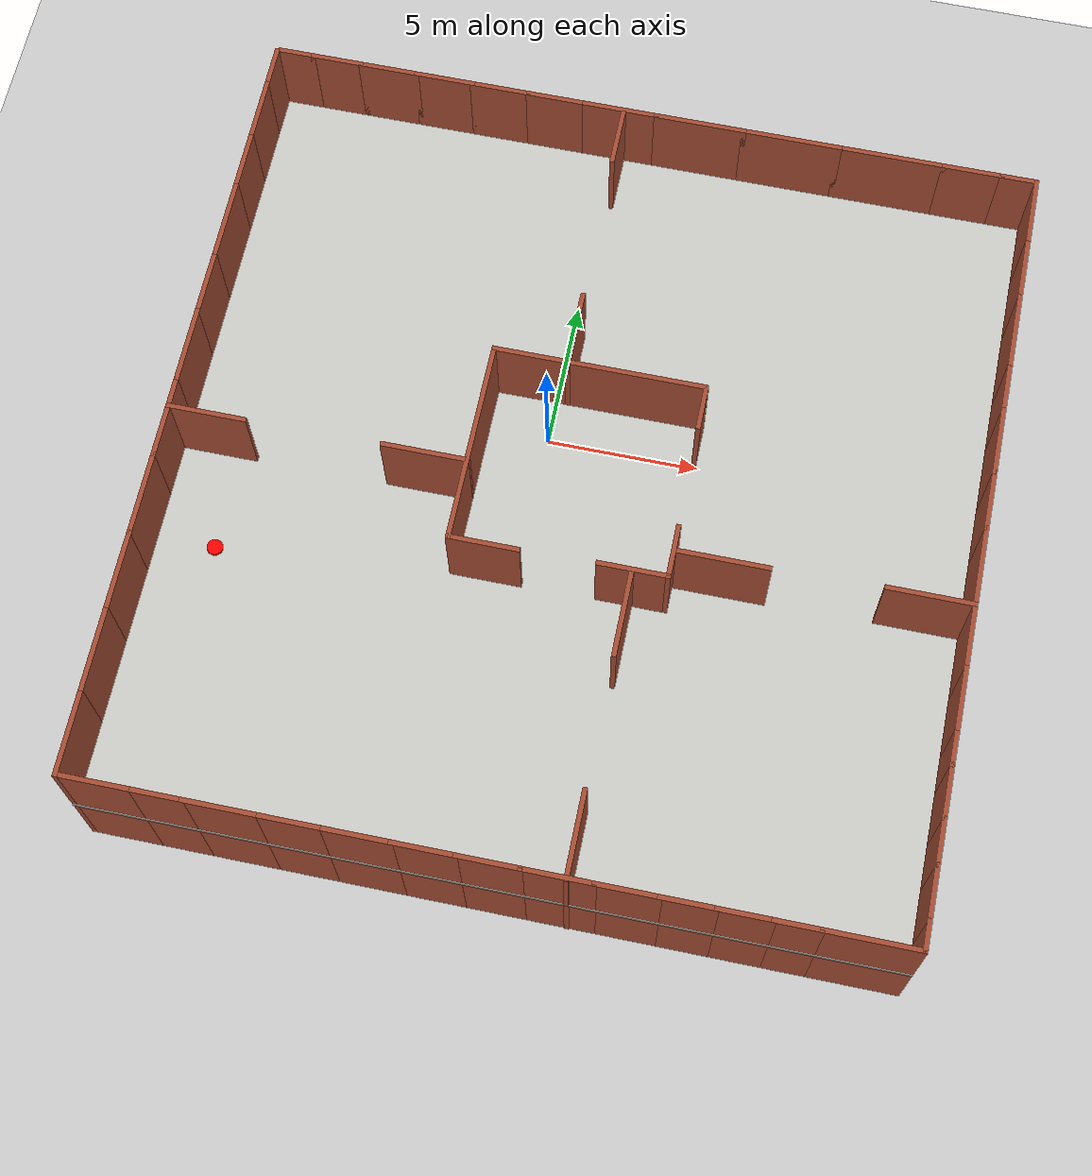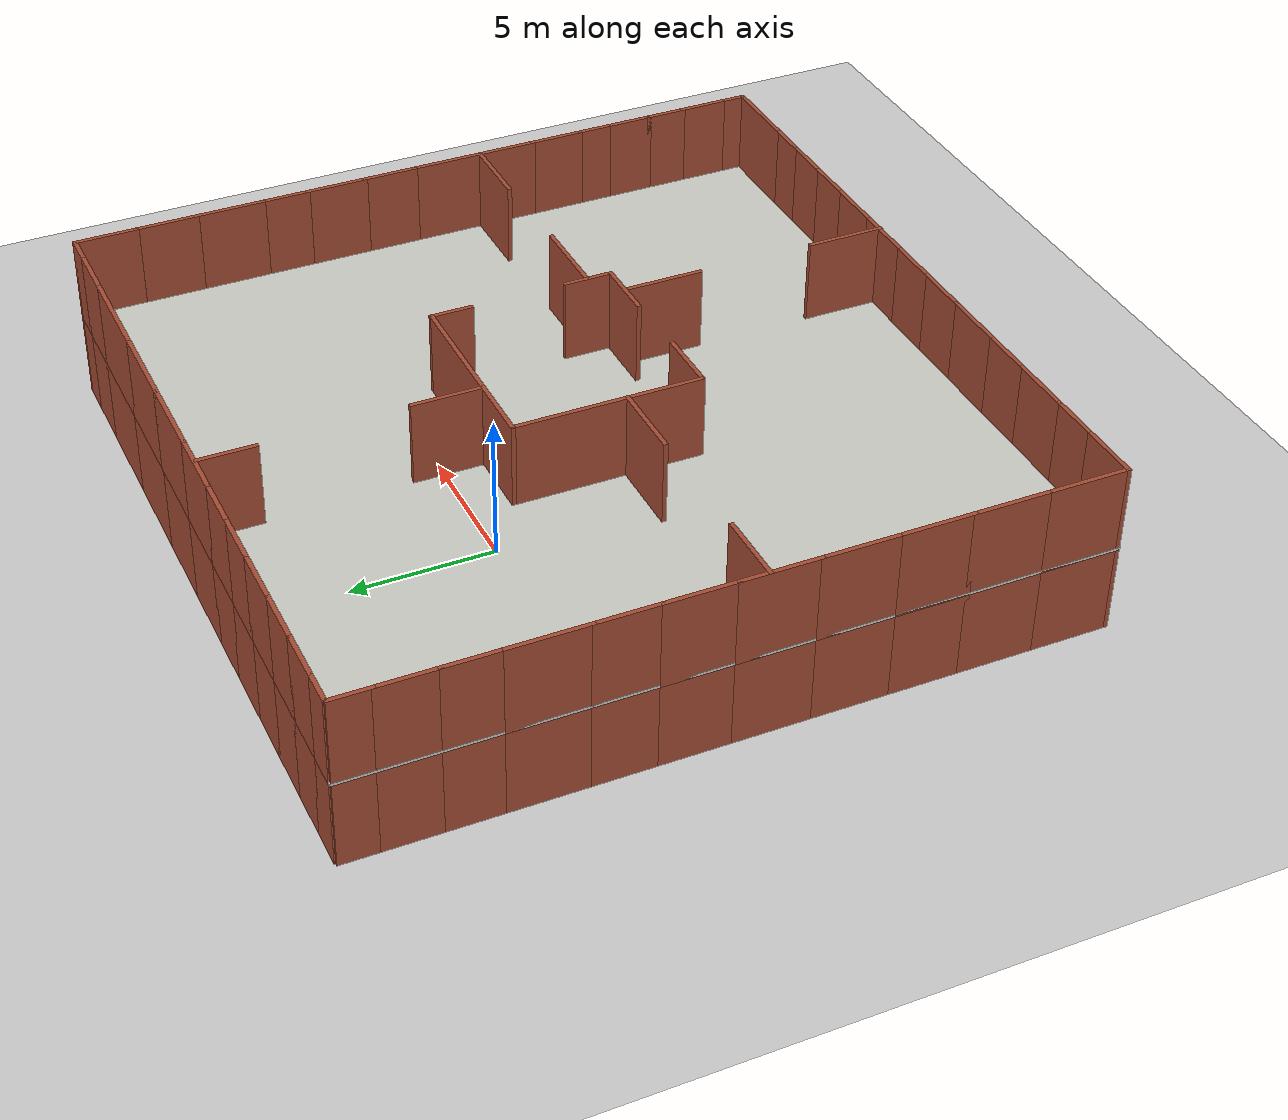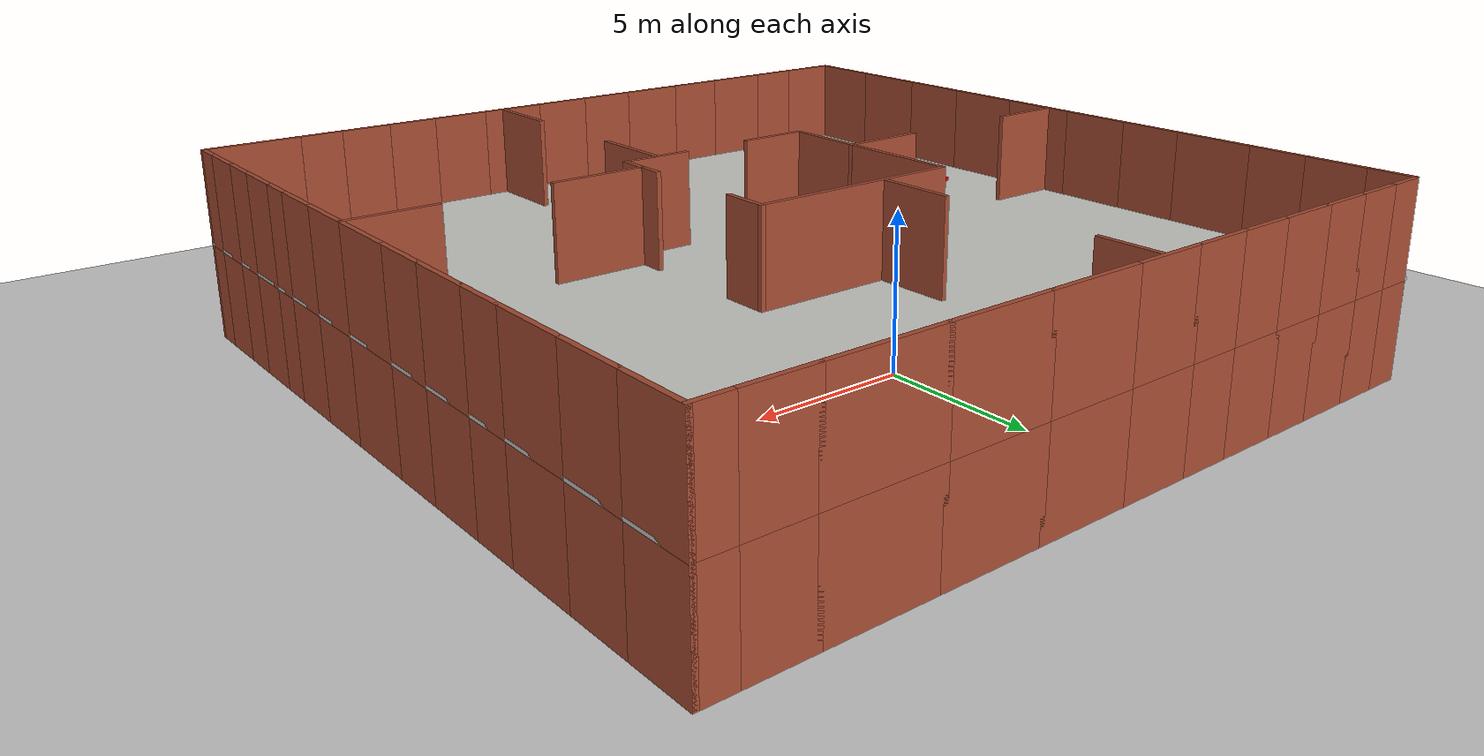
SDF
<sdf version="1.6">
 <world name="default">
  <light name="sun" type="directional">
   <pose>0 0 10 0 -0 0</pose>
   <diffuse>0.8 0.8 0.8 1</diffuse>
   <specular>0.2 0.2 0.2 1</specular>
   <attenuation>
    <range>1000</range>
    <constant>0.9</constant>
    <linear>0.01</linear>
    <quadratic>0.001</quadratic>
   </attenuation>
   <direction>-0.5 0.1 -0.9</direction>
   <spot><inner_angle>0</inner_angle><outer_angle>0</outer_angle><falloff>0</falloff></spot>
  </light>
  <model name="ground_plane">
   <static>1</static>
   <link name="link">
    <collision name="collision">
     <geometry><plane><normal>0 0 1</normal><size>100 100</size></plane></geometry>
     <surface><friction><ode><mu>100</mu><mu2>50</mu2></ode></friction></surface>
    </collision>
    <visual name="visual">
     <cast_shadows>0</cast_shadows>
     <geometry><plane><normal>0 0 1</normal><size>100 100</size></plane></geometry>
     <material>
      <script><uri>file://media/materials/scripts/gazebo.material</uri><name>Gazebo/Grey</name></script>
     </material>
    </visual>
   </link>
  </model>
  <gravity>0 0 -9.8</gravity>
  <magnetic_field>6e-06 2.3e-05 -4.2e-05</magnetic_field>
  <atmosphere type="adiabatic"/>
  <physics type="ode">
   <max_step_size>0.001</max_step_size>
   <real_time_factor>1</real_time_factor>
   <real_time_update_rate>1000</real_time_update_rate>
  </physics>
  <scene><ambient>0.4 0.4 0.4 1</ambient><background>0.7 0.7 0.7 1</background><shadows>1</shadows></scene>
  <spherical_coordinates>
   <surface_model>EARTH_WGS84</surface_model>
   <latitude_deg>0</latitude_deg>
   <longitude_deg>0</longitude_deg>
   <elevation>0</elevation>
   <heading_deg>0</heading_deg>
  </spherical_coordinates>
  <model name="bigMaze1">
   <pose>1.50484 -3.1802 0 0 -0 0</pose>
   <link name="Floor_1">
    <collision name="Floor_1_Collision">
     <geometry><box><size>24.95 25.0775 0.1</size></box></geometry>
     <pose>0 0 0.05 0 -0 0</pose>
    </collision>
    <visual name="Floor_1_Visual">
     <pose>0 0 0.05 0 -0 0</pose>
     <geometry><box><size>24.95 25.0775 0.1</size></box></geometry>
     <material>
      <script><uri>file://media/materials/scripts/gazebo.material</uri><name>Gazebo/CeilingTiled</name></script>
      <ambient>0.203922 0.396078 0.643137 1</ambient>
     </material>
     <meta><layer>1</layer></meta>
    </visual>
    <pose>-0 0 3 0 -0 0</pose>
   </link>
   <link name="Wall_10">
    <collision name="Wall_10_Collision">
     <geometry><box><size>2 0.15 3</size></box></geometry>
     <pose>0 0 1.5 0 -0 0</pose>
    </collision>
    <visual name="Wall_10_Visual">
     <pose>0 0 1.5 0 -0 0</pose>
     <geometry><box><size>2 0.15 3</size></box></geometry>
     <material>
      <script><uri>file://media/materials/scripts/gazebo.material</uri><name>Gazebo/Bricks</name></script>
      <ambient>1 1 1 1</ambient>
     </material>
     <meta><layer>0</layer></meta>
    </visual>
    <pose>-3.125 12.4638 0 0 -0 0</pose>
   </link>
   <link name="Wall_11">
    <collision name="Wall_11_Collision">
     <geometry><box><size>2.5 0.15 3</size></box></geometry>
     <pose>0 0 1.5 0 -0 0</pose>
    </collision>
    <visual name="Wall_11_Visual">
     <pose>0 0 1.5 0 -0 0</pose>
     <geometry><box><size>2.5 0.15 3</size></box></geometry>
     <material>
      <script><uri>file://media/materials/scripts/gazebo.material</uri><name>Gazebo/Bricks</name></script>
      <ambient>1 1 1 1</ambient>
     </material>
     <meta><layer>0</layer></meta>
    </visual>
    <pose>-1.025 12.4638 0 0 -0 0</pose>
   </link>
   <link name="Wall_12">
    <collision name="Wall_12_Collision">
     <geometry><box><size>3 0.15 3</size></box></geometry>
     <pose>0 0 1.5 0 -0 0</pose>
    </collision>
    <visual name="Wall_12_Visual">
     <pose>0 0 1.5 0 -0 0</pose>
     <geometry><box><size>3 0.15 3</size></box></geometry>
     <material>
      <script><uri>file://media/materials/scripts/gazebo.material</uri><name>Gazebo/Bricks</name></script>
      <ambient>1 1 1 1</ambient>
     </material>
     <meta><layer>0</layer></meta>
    </visual>
    <pose>1.575 12.4638 0 0 -0 0</pose>
   </link>
   <link name="Wall_13">
    <collision name="Wall_13_Collision">
     <geometry><box><size>3.25 0.15 3</size></box></geometry>
     <pose>0 0 1.5 0 -0 0</pose>
    </collision>
    <visual name="Wall_13_Visual">
     <pose>0 0 1.5 0 -0 0</pose>
     <geometry><box><size>3.25 0.15 3</size></box></geometry>
     <material>
      <script><uri>file://media/materials/scripts/gazebo.material</uri><name>Gazebo/Bricks</name></script>
      <ambient>1 1 1 1</ambient>
     </material>
     <meta><layer>0</layer></meta>
    </visual>
    <pose>4.55 12.4638 0 0 -0 0</pose>
   </link>
   <link name="Wall_14">
    <collision name="Wall_14_Collision">
     <geometry><box><size>3.5 0.15 3</size></box></geometry>
     <pose>0 0 1.5 0 -0 0</pose>
    </collision>
    <visual name="Wall_14_Visual">
     <pose>0 0 1.5 0 -0 0</pose>
     <geometry><box><size>3.5 0.15 3</size></box></geometry>
     <material>
      <script><uri>file://media/materials/scripts/gazebo.material</uri><name>Gazebo/Bricks</name></script>
      <ambient>1 1 1 1</ambient>
     </material>
     <meta><layer>0</layer></meta>
    </visual>
    <pose>7.775 12.4638 0 0 -0 0</pose>
   </link>
   <link name="Wall_149">
    <collision name="Wall_149_Collision">
     <geometry><box><size>1.25 0.15 3</size></box></geometry>
     <pose>0 0 1.5 0 -0 0</pose>
    </collision>
    <visual name="Wall_149_Visual">
     <pose>0 0 1.5 0 -0 0</pose>
     <geometry><box><size>1.25 0.15 3</size></box></geometry>
     <material>
      <script><uri>file://media/materials/scripts/gazebo.material</uri><name>Gazebo/Bricks</name></script>
      <ambient>1 1 1 1</ambient>
     </material>
     <meta><layer>1</layer></meta>
    </visual>
    <pose>-11.75 12.4638 3 0 -0 0</pose>
   </link>
   <link name="Wall_15">
    <collision name="Wall_15_Collision">
     <geometry><box><size>2 0.15 3</size></box></geometry>
     <pose>0 0 1.5 0 -0 0</pose>
    </collision>
    <visual name="Wall_15_Visual">
     <pose>0 0 1.5 0 -0 0</pose>
     <geometry><box><size>2 0.15 3</size></box></geometry>
     <material>
      <script><uri>file://media/materials/scripts/gazebo.material</uri><name>Gazebo/Bricks</name></script>
      <ambient>1 1 1 1</ambient>
     </material>
     <meta><layer>0</layer></meta>
    </visual>
    <pose>10.375 12.4638 0 0 -0 0</pose>
   </link>
   <link name="Wall_150">
    <collision name="Wall_150_Collision">
     <geometry><box><size>1.75 0.15 3</size></box></geometry>
     <pose>0 0 1.5 0 -0 0</pose>
    </collision>
    <visual name="Wall_150_Visual">
     <pose>0 0 1.5 0 -0 0</pose>
     <geometry><box><size>1.75 0.15 3</size></box></geometry>
     <material>
      <script><uri>file://media/materials/scripts/gazebo.material</uri><name>Gazebo/Bricks</name></script>
      <ambient>1 1 1 1</ambient>
     </material>
     <meta><layer>1</layer></meta>
    </visual>
    <pose>-10.4 12.4638 3 0 -0 0</pose>
   </link>
   <link name="Wall_151">
    <collision name="Wall_151_Collision">
     <geometry><box><size>2 0.15 3</size></box></geometry>
     <pose>0 0 1.5 0 -0 0</pose>
    </collision>
    <visual name="Wall_151_Visual">
     <pose>0 0 1.5 0 -0 0</pose>
     <geometry><box><size>2 0.15 3</size></box></geometry>
     <material>
      <script><uri>file://media/materials/scripts/gazebo.material</uri><name>Gazebo/Bricks</name></script>
      <ambient>1 1 1 1</ambient>
     </material>
     <meta><layer>1</layer></meta>
    </visual>
    <pose>-8.675 12.4638 3 0 -0 0</pose>
   </link>
   <link name="Wall_152">
    <collision name="Wall_152_Collision">
     <geometry><box><size>2 0.15 3</size></box></geometry>
     <pose>0 0 1.5 0 -0 0</pose>
    </collision>
    <visual name="Wall_152_Visual">
     <pose>0 0 1.5 0 -0 0</pose>
     <geometry><box><size>2 0.15 3</size></box></geometry>
     <material>
      <script><uri>file://media/materials/scripts/gazebo.material</uri><name>Gazebo/Bricks</name></script>
      <ambient>1 1 1 1</ambient>
     </material>
     <meta><layer>1</layer></meta>
    </visual>
    <pose>-6.825 12.4638 3 0 -0 0</pose>
   </link>
   <link name="Wall_153">
    <collision name="Wall_153_Collision">
     <geometry><box><size>2 0.15 3</size></box></geometry>
     <pose>0 0 1.5 0 -0 0</pose>
    </collision>
    <visual name="Wall_153_Visual">
     <pose>0 0 1.5 0 -0 0</pose>
     <geometry><box><size>2 0.15 3</size></box></geometry>
     <material>
      <script><uri>file://media/materials/scripts/gazebo.material</uri><name>Gazebo/Bricks</name></script>
      <ambient>1 1 1 1</ambient>
     </material>
     <meta><layer>1</layer></meta>
    </visual>
    <pose>-4.975 12.4638 3 0 -0 0</pose>
   </link>
   <link name="Wall_154">
    <collision name="Wall_154_Collision">
     <geometry><box><size>2 0.15 3</size></box></geometry>
     <pose>0 0 1.5 0 -0 0</pose>
    </collision>
    <visual name="Wall_154_Visual">
     <pose>0 0 1.5 0 -0 0</pose>
     <geometry><box><size>2 0.15 3</size></box></geometry>
     <material>
      <script><uri>file://media/materials/scripts/gazebo.material</uri><name>Gazebo/Bricks</name></script>
      <ambient>1 1 1 1</ambient>
     </material>
     <meta><layer>1</layer></meta>
    </visual>
    <pose>-3.125 12.4638 3 0 -0 0</pose>
   </link>
   <link name="Wall_155">
    <collision name="Wall_155_Collision">
     <geometry><box><size>2.5 0.15 3</size></box></geometry>
     <pose>0 0 1.5 0 -0 0</pose>
    </collision>
    <visual name="Wall_155_Visual">
     <pose>0 0 1.5 0 -0 0</pose>
     <geometry><box><size>2.5 0.15 3</size></box></geometry>
     <material>
      <script><uri>file://media/materials/scripts/gazebo.material</uri><name>Gazebo/Bricks</name></script>
      <ambient>1 1 1 1</ambient>
     </material>
     <meta><layer>1</layer></meta>
    </visual>
    <pose>-1.025 12.4638 3 0 -0 0</pose>
   </link>
   <link name="Wall_156">
    <collision name="Wall_156_Collision">
     <geometry><box><size>3 0.15 3</size></box></geometry>
     <pose>0 0 1.5 0 -0 0</pose>
    </collision>
    <visual name="Wall_156_Visual">
     <pose>0 0 1.5 0 -0 0</pose>
     <geometry><box><size>3 0.15 3</size></box></geometry>
     <material>
      <script><uri>file://media/materials/scripts/gazebo.material</uri><name>Gazebo/Bricks</name></script>
      <ambient>1 1 1 1</ambient>
     </material>
     <meta><layer>1</layer></meta>
    </visual>
    <pose>1.575 12.4638 3 0 -0 0</pose>
   </link>
   <link name="Wall_157">
    <collision name="Wall_157_Collision">
     <geometry><box><size>3.25 0.15 3</size></box></geometry>
     <pose>0 0 1.5 0 -0 0</pose>
    </collision>
    <visual name="Wall_157_Visual">
     <pose>0 0 1.5 0 -0 0</pose>
     <geometry><box><size>3.25 0.15 3</size></box></geometry>
     <material>
      <script><uri>file://media/materials/scripts/gazebo.material</uri><name>Gazebo/Bricks</name></script>
      <ambient>1 1 1 1</ambient>
     </material>
     <meta><layer>1</layer></meta>
    </visual>
    <pose>4.55 12.4638 3 0 -0 0</pose>
   </link>
   <link name="Wall_158">
    <collision name="Wall_158_Collision">
     <geometry><box><size>3.5 0.15 3</size></box></geometry>
     <pose>0 0 1.5 0 -0 0</pose>
    </collision>
    <visual name="Wall_158_Visual">
     <pose>0 0 1.5 0 -0 0</pose>
     <geometry><box><size>3.5 0.15 3</size></box></geometry>
     <material>
      <script><uri>file://media/materials/scripts/gazebo.material</uri><name>Gazebo/Bricks</name></script>
      <ambient>1 1 1 1</ambient>
     </material>
     <meta><layer>1</layer></meta>
    </visual>
    <pose>7.775 12.4638 3 0 -0 0</pose>
   </link>
   <link name="Wall_159">
    <collision name="Wall_159_Collision">
     <geometry><box><size>2 0.15 3</size></box></geometry>
     <pose>0 0 1.5 0 -0 0</pose>
    </collision>
    <visual name="Wall_159_Visual">
     <pose>0 0 1.5 0 -0 0</pose>
     <geometry><box><size>2 0.15 3</size></box></geometry>
     <material>
      <script><uri>file://media/materials/scripts/gazebo.material</uri><name>Gazebo/Bricks</name></script>
      <ambient>1 1 1 1</ambient>
     </material>
     <meta><layer>1</layer></meta>
    </visual>
    <pose>10.375 12.4638 3 0 -0 0</pose>
   </link>
   <link name="Wall_16">
    <collision name="Wall_16_Collision">
     <geometry><box><size>1.25 0.15 3</size></box></geometry>
     <pose>0 0 1.5 0 -0 0</pose>
    </collision>
    <visual name="Wall_16_Visual">
     <pose>0 0 1.5 0 -0 0</pose>
     <geometry><box><size>1.25 0.15 3</size></box></geometry>
     <material>
      <script><uri>file://media/materials/scripts/gazebo.material</uri><name>Gazebo/Bricks</name></script>
      <ambient>1 1 1 1</ambient>
     </material>
     <meta><layer>0</layer></meta>
    </visual>
    <pose>11.85 12.4638 0 0 -0 0</pose>
   </link>
   <link name="Wall_160">
    <collision name="Wall_160_Collision">
     <geometry><box><size>1.25 0.15 3</size></box></geometry>
     <pose>0 0 1.5 0 -0 0</pose>
    </collision>
    <visual name="Wall_160_Visual">
     <pose>0 0 1.5 0 -0 0</pose>
     <geometry><box><size>1.25 0.15 3</size></box></geometry>
     <material>
      <script><uri>file://media/materials/scripts/gazebo.material</uri><name>Gazebo/Bricks</name></script>
      <ambient>1 1 1 1</ambient>
     </material>
     <meta><layer>1</layer></meta>
    </visual>
    <pose>11.85 12.4638 3 0 -0 0</pose>
   </link>
   <link name="Wall_161">
    <collision name="Wall_161_Collision">
     <geometry><box><size>2.25 0.15 3</size></box></geometry>
     <pose>0 0 1.5 0 -0 0</pose>
    </collision>
    <visual name="Wall_161_Visual">
     <pose>0 0 1.5 0 -0 0</pose>
     <geometry><box><size>2.25 0.15 3</size></box></geometry>
     <material>
      <script><uri>file://media/materials/scripts/gazebo.material</uri><name>Gazebo/Bricks</name></script>
      <ambient>1 1 1 1</ambient>
     </material>
     <meta><layer>1</layer></meta>
    </visual>
    <pose>12.4 11.4138 3 0 -0 -1.5708</pose>
   </link>
   <link name="Wall_162">
    <collision name="Wall_162_Collision">
     <geometry><box><size>2.25 0.15 3</size></box></geometry>
     <pose>0 0 1.5 0 -0 0</pose>
    </collision>
    <visual name="Wall_162_Visual">
     <pose>0 0 1.5 0 -0 0</pose>
     <geometry><box><size>2.25 0.15 3</size></box></geometry>
     <material>
      <script><uri>file://media/materials/scripts/gazebo.material</uri><name>Gazebo/Bricks</name></script>
      <ambient>1 1 1 1</ambient>
     </material>
     <meta><layer>1</layer></meta>
    </visual>
    <pose>12.4 9.31377 3 0 -0 -1.5708</pose>
   </link>
   <link name="Wall_163">
    <collision name="Wall_163_Collision">
     <geometry><box><size>2.5 0.15 3</size></box></geometry>
     <pose>0 0 1.5 0 -0 0</pose>
    </collision>
    <visual name="Wall_163_Visual">
     <pose>0 0 1.5 0 -0 0</pose>
     <geometry><box><size>2.5 0.15 3</size></box></geometry>
     <material>
      <script><uri>file://media/materials/scripts/gazebo.material</uri><name>Gazebo/Bricks</name></script>
      <ambient>1 1 1 1</ambient>
     </material>
     <meta><layer>1</layer></meta>
    </visual>
    <pose>12.4 7.08877 3 0 -0 -1.5708</pose>
   </link>
   <link name="Wall_164">
    <collision name="Wall_164_Collision">
     <geometry><box><size>1.75 0.15 3</size></box></geometry>
     <pose>0 0 1.5 0 -0 0</pose>
    </collision>
    <visual name="Wall_164_Visual">
     <pose>0 0 1.5 0 -0 0</pose>
     <geometry><box><size>1.75 0.15 3</size></box></geometry>
     <material>
      <script><uri>file://media/materials/scripts/gazebo.material</uri><name>Gazebo/Bricks</name></script>
      <ambient>1 1 1 1</ambient>
     </material>
     <meta><layer>1</layer></meta>
    </visual>
    <pose>12.4 5.11376 3 0 -0 -1.5708</pose>
   </link>
   <link name="Wall_165">
    <collision name="Wall_165_Collision">
     <geometry><box><size>2.25 0.15 3</size></box></geometry>
     <pose>0 0 1.5 0 -0 0</pose>
    </collision>
    <visual name="Wall_165_Visual">
     <pose>0 0 1.5 0 -0 0</pose>
     <geometry><box><size>2.25 0.15 3</size></box></geometry>
     <material>
      <script><uri>file://media/materials/scripts/gazebo.material</uri><name>Gazebo/Bricks</name></script>
      <ambient>1 1 1 1</ambient>
     </material>
     <meta><layer>1</layer></meta>
    </visual>
    <pose>12.4 3.26376 3 0 -0 -1.5708</pose>
   </link>
   <link name="Wall_166">
    <collision name="Wall_166_Collision">
     <geometry><box><size>2 0.15 3</size></box></geometry>
     <pose>0 0 1.5 0 -0 0</pose>
    </collision>
    <visual name="Wall_166_Visual">
     <pose>0 0 1.5 0 -0 0</pose>
     <geometry><box><size>2 0.15 3</size></box></geometry>
     <material>
      <script><uri>file://media/materials/scripts/gazebo.material</uri><name>Gazebo/Bricks</name></script>
      <ambient>1 1 1 1</ambient>
     </material>
     <meta><layer>1</layer></meta>
    </visual>
    <pose>12.4 1.28876 3 0 -0 -1.5708</pose>
   </link>
   <link name="Wall_167">
    <collision name="Wall_167_Collision">
     <geometry><box><size>2.60701 0.15 3</size></box></geometry>
     <pose>0 0 1.5 0 -0 0</pose>
    </collision>
    <visual name="Wall_167_Visual">
     <pose>0 0 1.5 0 -0 0</pose>
     <geometry><box><size>2.60701 0.15 3</size></box></geometry>
     <material>
      <script><uri>file://media/materials/scripts/gazebo.material</uri><name>Gazebo/Bricks</name></script>
      <ambient>1 1 1 1</ambient>
     </material>
     <meta><layer>1</layer></meta>
    </visual>
    <pose>12.4 -0.864741 3 0 -0 -1.5708</pose>
   </link>
   <link name="Wall_168">
    <collision name="Wall_168_Collision">
     <geometry><box><size>2.14299 0.15 3</size></box></geometry>
     <pose>0 0 1.5 0 -0 0</pose>
    </collision>
    <visual name="Wall_168_Visual">
     <pose>0 0 1.5 0 -0 0</pose>
     <geometry><box><size>2.14299 0.15 3</size></box></geometry>
     <material>
      <script><uri>file://media/materials/scripts/gazebo.material</uri><name>Gazebo/Bricks</name></script>
      <ambient>1 1 1 1</ambient>
     </material>
     <meta><layer>1</layer></meta>
    </visual>
    <pose>12.4 -3.08974 3 0 -0 -1.5708</pose>
   </link>
   <link name="Wall_169">
    <collision name="Wall_169_Collision">
     <geometry><box><size>2 0.15 3</size></box></geometry>
     <pose>0 0 1.5 0 -0 0</pose>
    </collision>
    <visual name="Wall_169_Visual">
     <pose>0 0 1.5 0 -0 0</pose>
     <geometry><box><size>2 0.15 3</size></box></geometry>
     <material>
      <script><uri>file://media/materials/scripts/gazebo.material</uri><name>Gazebo/Bricks</name></script>
      <ambient>1 1 1 1</ambient>
     </material>
     <meta><layer>1</layer></meta>
    </visual>
    <pose>12.4 -5.01124 3 0 -0 -1.5708</pose>
   </link>
   <link name="Wall_17">
    <collision name="Wall_17_Collision">
     <geometry><box><size>2.25 0.15 3</size></box></geometry>
     <pose>0 0 1.5 0 -0 0</pose>
    </collision>
    <visual name="Wall_17_Visual">
     <pose>0 0 1.5 0 -0 0</pose>
     <geometry><box><size>2.25 0.15 3</size></box></geometry>
     <material>
      <script><uri>file://media/materials/scripts/gazebo.material</uri><name>Gazebo/Bricks</name></script>
      <ambient>1 1 1 1</ambient>
     </material>
     <meta><layer>0</layer></meta>
    </visual>
    <pose>12.4 11.4138 0 0 -0 -1.5708</pose>
   </link>
   <link name="Wall_170">
    <collision name="Wall_170_Collision">
     <geometry><box><size>1.25 0.15 3</size></box></geometry>
     <pose>0 0 1.5 0 -0 0</pose>
    </collision>
    <visual name="Wall_170_Visual">
     <pose>0 0 1.5 0 -0 0</pose>
     <geometry><box><size>1.25 0.15 3</size></box></geometry>
     <material>
      <script><uri>file://media/materials/scripts/gazebo.material</uri><name>Gazebo/Bricks</name></script>
      <ambient>1 1 1 1</ambient>
     </material>
     <meta><layer>1</layer></meta>
    </visual>
    <pose>12.4 -6.48623 3 0 -0 -1.5708</pose>
   </link>
   <link name="Wall_171">
    <collision name="Wall_171_Collision">
     <geometry><box><size>1.75 0.15 3</size></box></geometry>
     <pose>0 0 1.5 0 -0 0</pose>
    </collision>
    <visual name="Wall_171_Visual">
     <pose>0 0 1.5 0 -0 0</pose>
     <geometry><box><size>1.75 0.15 3</size></box></geometry>
     <material>
      <script><uri>file://media/materials/scripts/gazebo.material</uri><name>Gazebo/Bricks</name></script>
      <ambient>1 1 1 1</ambient>
     </material>
     <meta><layer>1</layer></meta>
    </visual>
    <pose>12.4 -7.83624 3 0 -0 -1.5708</pose>
   </link>
   <link name="Wall_172">
    <collision name="Wall_172_Collision">
     <geometry><box><size>1.5 0.15 3</size></box></geometry>
     <pose>0 0 1.5 0 -0 0</pose>
    </collision>
    <visual name="Wall_172_Visual">
     <pose>0 0 1.5 0 -0 0</pose>
     <geometry><box><size>1.5 0.15 3</size></box></geometry>
     <material>
      <script><uri>file://media/materials/scripts/gazebo.material</uri><name>Gazebo/Bricks</name></script>
      <ambient>1 1 1 1</ambient>
     </material>
     <meta><layer>1</layer></meta>
    </visual>
    <pose>12.4 -9.31123 3 0 -0 -1.5708</pose>
   </link>
   <link name="Wall_173">
    <collision name="Wall_173_Collision">
     <geometry><box><size>1.75 0.15 3</size></box></geometry>
     <pose>0 0 1.5 0 -0 0</pose>
    </collision>
    <visual name="Wall_173_Visual">
     <pose>0 0 1.5 0 -0 0</pose>
     <geometry><box><size>1.75 0.15 3</size></box></geometry>
     <material>
      <script><uri>file://media/materials/scripts/gazebo.material</uri><name>Gazebo/Bricks</name></script>
      <ambient>1 1 1 1</ambient>
     </material>
     <meta><layer>1</layer></meta>
    </visual>
    <pose>12.4 -10.7862 3 0 -0 -1.5708</pose>
   </link>
   <link name="Wall_174">
    <collision name="Wall_174_Collision">
     <geometry><box><size>1 0.15 3</size></box></geometry>
     <pose>0 0 1.5 0 -0 0</pose>
    </collision>
    <visual name="Wall_174_Visual">
     <pose>0 0 1.5 0 -0 0</pose>
     <geometry><box><size>1 0.15 3</size></box></geometry>
     <material>
      <script><uri>file://media/materials/scripts/gazebo.material</uri><name>Gazebo/Bricks</name></script>
      <ambient>1 1 1 1</ambient>
     </material>
     <meta><layer>1</layer></meta>
    </visual>
    <pose>12.4 -12.0112 3 0 -0 -1.5708</pose>
   </link>
   <link name="Wall_175">
    <collision name="Wall_175_Collision">
     <geometry><box><size>3 0.15 3</size></box></geometry>
     <pose>0 0 1.5 0 -0 0</pose>
    </collision>
    <visual name="Wall_175_Visual">
     <pose>0 0 1.5 0 -0 0</pose>
     <geometry><box><size>3 0.15 3</size></box></geometry>
     <material>
      <script><uri>file://media/materials/scripts/gazebo.material</uri><name>Gazebo/Bricks</name></script>
      <ambient>1 1 1 1</ambient>
     </material>
     <meta><layer>1</layer></meta>
    </visual>
    <pose>10.975 -12.4362 3 0 -0 3.14159</pose>
   </link>
   <link name="Wall_176">
    <collision name="Wall_176_Collision">
     <geometry><box><size>1.5 0.15 3</size></box></geometry>
     <pose>0 0 1.5 0 -0 0</pose>
    </collision>
    <visual name="Wall_176_Visual">
     <pose>0 0 1.5 0 -0 0</pose>
     <geometry><box><size>1.5 0.15 3</size></box></geometry>
     <material>
      <script><uri>file://media/materials/scripts/gazebo.material</uri><name>Gazebo/Bricks</name></script>
      <ambient>1 1 1 1</ambient>
     </material>
     <meta><layer>1</layer></meta>
    </visual>
    <pose>8.875 -12.4362 3 0 -0 3.14159</pose>
   </link>
   <link name="Wall_177">
    <collision name="Wall_177_Collision">
     <geometry><box><size>1.75 0.15 3</size></box></geometry>
     <pose>0 0 1.5 0 -0 0</pose>
    </collision>
    <visual name="Wall_177_Visual">
     <pose>0 0 1.5 0 -0 0</pose>
     <geometry><box><size>1.75 0.15 3</size></box></geometry>
     <material>
      <script><uri>file://media/materials/scripts/gazebo.material</uri><name>Gazebo/Bricks</name></script>
      <ambient>1 1 1 1</ambient>
     </material>
     <meta><layer>1</layer></meta>
    </visual>
    <pose>7.4 -12.4362 3 0 -0 3.14159</pose>
   </link>
   <link name="Wall_178">
    <collision name="Wall_178_Collision">
     <geometry><box><size>1.75 0.15 3</size></box></geometry>
     <pose>0 0 1.5 0 -0 0</pose>
    </collision>
    <visual name="Wall_178_Visual">
     <pose>0 0 1.5 0 -0 0</pose>
     <geometry><box><size>1.75 0.15 3</size></box></geometry>
     <material>
      <script><uri>file://media/materials/scripts/gazebo.material</uri><name>Gazebo/Bricks</name></script>
      <ambient>1 1 1 1</ambient>
     </material>
     <meta><layer>1</layer></meta>
    </visual>
    <pose>5.8 -12.4362 3 0 -0 3.14159</pose>
   </link>
   <link name="Wall_179">
    <collision name="Wall_179_Collision">
     <geometry><box><size>2 0.15 3</size></box></geometry>
     <pose>0 0 1.5 0 -0 0</pose>
    </collision>
    <visual name="Wall_179_Visual">
     <pose>0 0 1.5 0 -0 0</pose>
     <geometry><box><size>2 0.15 3</size></box></geometry>
     <material>
      <script><uri>file://media/materials/scripts/gazebo.material</uri><name>Gazebo/Bricks</name></script>
      <ambient>1 1 1 1</ambient>
     </material>
     <meta><layer>1</layer></meta>
    </visual>
    <pose>4.075 -12.4362 3 0 -0 3.14159</pose>
   </link>
   <link name="Wall_18">
    <collision name="Wall_18_Collision">
     <geometry><box><size>2.25 0.15 3</size></box></geometry>
     <pose>0 0 1.5 0 -0 0</pose>
    </collision>
    <visual name="Wall_18_Visual">
     <pose>0 0 1.5 0 -0 0</pose>
     <geometry><box><size>2.25 0.15 3</size></box></geometry>
     <material>
      <script><uri>file://media/materials/scripts/gazebo.material</uri><name>Gazebo/Bricks</name></script>
      <ambient>1 1 1 1</ambient>
     </material>
     <meta><layer>0</layer></meta>
    </visual>
    <pose>12.4 9.31377 0 0 -0 -1.5708</pose>
   </link>
   <link name="Wall_180">
    <collision name="Wall_180_Collision">
     <geometry><box><size>2.25 0.15 3</size></box></geometry>
     <pose>0 0 1.5 0 -0 0</pose>
    </collision>
    <visual name="Wall_180_Visual">
     <pose>0 0 1.5 0 -0 0</pose>
     <geometry><box><size>2.25 0.15 3</size></box></geometry>
     <material>
      <script><uri>file://media/materials/scripts/gazebo.material</uri><name>Gazebo/Bricks</name></script>
      <ambient>1 1 1 1</ambient>
     </material>
     <meta><layer>1</layer></meta>
    </visual>
    <pose>2.1 -12.4362 3 0 -0 3.14159</pose>
   </link>
   <link name="Wall_181">
    <collision name="Wall_181_Collision">
     <geometry><box><size>2 0.15 3</size></box></geometry>
     <pose>0 0 1.5 0 -0 0</pose>
    </collision>
    <visual name="Wall_181_Visual">
     <pose>0 0 1.5 0 -0 0</pose>
     <geometry><box><size>2 0.15 3</size></box></geometry>
     <material>
      <script><uri>file://media/materials/scripts/gazebo.material</uri><name>Gazebo/Bricks</name></script>
      <ambient>1 1 1 1</ambient>
     </material>
     <meta><layer>1</layer></meta>
    </visual>
    <pose>0.125 -12.4362 3 0 -0 3.14159</pose>
   </link>
   <link name="Wall_182">
    <collision name="Wall_182_Collision">
     <geometry><box><size>2 0.15 3</size></box></geometry>
     <pose>0 0 1.5 0 -0 0</pose>
    </collision>
    <visual name="Wall_182_Visual">
     <pose>0 0 1.5 0 -0 0</pose>
     <geometry><box><size>2 0.15 3</size></box></geometry>
     <material>
      <script><uri>file://media/materials/scripts/gazebo.material</uri><name>Gazebo/Bricks</name></script>
      <ambient>1 1 1 1</ambient>
     </material>
     <meta><layer>1</layer></meta>
    </visual>
    <pose>-1.725 -12.4362 3 0 -0 3.14159</pose>
   </link>
   <link name="Wall_183">
    <collision name="Wall_183_Collision">
     <geometry><box><size>2.25 0.15 3</size></box></geometry>
     <pose>0 0 1.5 0 -0 0</pose>
    </collision>
    <visual name="Wall_183_Visual">
     <pose>0 0 1.5 0 -0 0</pose>
     <geometry><box><size>2.25 0.15 3</size></box></geometry>
     <material>
      <script><uri>file://media/materials/scripts/gazebo.material</uri><name>Gazebo/Bricks</name></script>
      <ambient>1 1 1 1</ambient>
     </material>
     <meta><layer>1</layer></meta>
    </visual>
    <pose>-3.7 -12.4362 3 0 -0 3.14159</pose>
   </link>
   <link name="Wall_184">
    <collision name="Wall_184_Collision">
     <geometry><box><size>2 0.15 3</size></box></geometry>
     <pose>0 0 1.5 0 -0 0</pose>
    </collision>
    <visual name="Wall_184_Visual">
     <pose>0 0 1.5 0 -0 0</pose>
     <geometry><box><size>2 0.15 3</size></box></geometry>
     <material>
      <script><uri>file://media/materials/scripts/gazebo.material</uri><name>Gazebo/Bricks</name></script>
      <ambient>1 1 1 1</ambient>
     </material>
     <meta><layer>1</layer></meta>
    </visual>
    <pose>-5.675 -12.4362 3 0 -0 3.14159</pose>
   </link>
   <link name="Wall_185">
    <collision name="Wall_185_Collision">
     <geometry><box><size>2.25 0.15 3</size></box></geometry>
     <pose>0 0 1.5 0 -0 0</pose>
    </collision>
    <visual name="Wall_185_Visual">
     <pose>0 0 1.5 0 -0 0</pose>
     <geometry><box><size>2.25 0.15 3</size></box></geometry>
     <material>
      <script><uri>file://media/materials/scripts/gazebo.material</uri><name>Gazebo/Bricks</name></script>
      <ambient>1 1 1 1</ambient>
     </material>
     <meta><layer>1</layer></meta>
    </visual>
    <pose>-7.65 -12.4362 3 0 -0 3.14159</pose>
   </link>
   <link name="Wall_186">
    <collision name="Wall_186_Collision">
     <geometry><box><size>1.75 0.15 3</size></box></geometry>
     <pose>0 0 1.5 0 -0 0</pose>
    </collision>
    <visual name="Wall_186_Visual">
     <pose>0 0 1.5 0 -0 0</pose>
     <geometry><box><size>1.75 0.15 3</size></box></geometry>
     <material>
      <script><uri>file://media/materials/scripts/gazebo.material</uri><name>Gazebo/Bricks</name></script>
      <ambient>1 1 1 1</ambient>
     </material>
     <meta><layer>1</layer></meta>
    </visual>
    <pose>-9.5 -12.4362 3 0 -0 3.14159</pose>
   </link>
   <link name="Wall_187">
    <collision name="Wall_187_Collision">
     <geometry><box><size>2.25 0.15 3</size></box></geometry>
     <pose>0 0 1.5 0 -0 0</pose>
    </collision>
    <visual name="Wall_187_Visual">
     <pose>0 0 1.5 0 -0 0</pose>
     <geometry><box><size>2.25 0.15 3</size></box></geometry>
     <material>
      <script><uri>file://media/materials/scripts/gazebo.material</uri><name>Gazebo/Bricks</name></script>
      <ambient>1 1 1 1</ambient>
     </material>
     <meta><layer>1</layer></meta>
    </visual>
    <pose>-11.35 -12.4362 3 0 -0 3.14159</pose>
   </link>
   <link name="Wall_188">
    <collision name="Wall_188_Collision">
     <geometry><box><size>2.75 0.15 3</size></box></geometry>
     <pose>0 0 1.5 0 -0 0</pose>
    </collision>
    <visual name="Wall_188_Visual">
     <pose>0 0 1.5 0 -0 0</pose>
     <geometry><box><size>2.75 0.15 3</size></box></geometry>
     <material>
      <script><uri>file://media/materials/scripts/gazebo.material</uri><name>Gazebo/Bricks</name></script>
      <ambient>1 1 1 1</ambient>
     </material>
     <meta><layer>1</layer></meta>
    </visual>
    <pose>-12.4 -11.1362 3 0 -0 1.5708</pose>
   </link>
   <link name="Wall_189">
    <collision name="Wall_189_Collision">
     <geometry><box><size>2.75 0.15 3</size></box></geometry>
     <pose>0 0 1.5 0 -0 0</pose>
    </collision>
    <visual name="Wall_189_Visual">
     <pose>0 0 1.5 0 -0 0</pose>
     <geometry><box><size>2.75 0.15 3</size></box></geometry>
     <material>
      <script><uri>file://media/materials/scripts/gazebo.material</uri><name>Gazebo/Bricks</name></script>
      <ambient>1 1 1 1</ambient>
     </material>
     <meta><layer>1</layer></meta>
    </visual>
    <pose>-12.4 -8.53623 3 0 -0 1.5708</pose>
   </link>
   <link name="Wall_19">
    <collision name="Wall_19_Collision">
     <geometry><box><size>2.5 0.15 3</size></box></geometry>
     <pose>0 0 1.5 0 -0 0</pose>
    </collision>
    <visual name="Wall_19_Visual">
     <pose>0 0 1.5 0 -0 0</pose>
     <geometry><box><size>2.5 0.15 3</size></box></geometry>
     <material>
      <script><uri>file://media/materials/scripts/gazebo.material</uri><name>Gazebo/Bricks</name></script>
      <ambient>1 1 1 1</ambient>
     </material>
     <meta><layer>0</layer></meta>
    </visual>
    <pose>12.4 7.08877 0 0 -0 -1.5708</pose>
   </link>
   <link name="Wall_190">
    <collision name="Wall_190_Collision">
     <geometry><box><size>2.5 0.15 3</size></box></geometry>
     <pose>0 0 1.5 0 -0 0</pose>
    </collision>
    <visual name="Wall_190_Visual">
     <pose>0 0 1.5 0 -0 0</pose>
     <geometry><box><size>2.5 0.15 3</size></box></geometry>
     <material>
      <script><uri>file://media/materials/scripts/gazebo.material</uri><name>Gazebo/Bricks</name></script>
      <ambient>1 1 1 1</ambient>
     </material>
     <meta><layer>1</layer></meta>
    </visual>
    <pose>-12.4 -6.06123 3 0 -0 1.5708</pose>
   </link>
   <link name="Wall_191">
    <collision name="Wall_191_Collision">
     <geometry><box><size>2.75 0.15 3</size></box></geometry>
     <pose>0 0 1.5 0 -0 0</pose>
    </collision>
    <visual name="Wall_191_Visual">
     <pose>0 0 1.5 0 -0 0</pose>
     <geometry><box><size>2.75 0.15 3</size></box></geometry>
     <material>
      <script><uri>file://media/materials/scripts/gazebo.material</uri><name>Gazebo/Bricks</name></script>
      <ambient>1 1 1 1</ambient>
     </material>
     <meta><layer>1</layer></meta>
    </visual>
    <pose>-12.4 -3.58623 3 0 -0 1.5708</pose>
   </link>
   <link name="Wall_192">
    <collision name="Wall_192_Collision">
     <geometry><box><size>2.75 0.15 3</size></box></geometry>
     <pose>0 0 1.5 0 -0 0</pose>
    </collision>
    <visual name="Wall_192_Visual">
     <pose>0 0 1.5 0 -0 0</pose>
     <geometry><box><size>2.75 0.15 3</size></box></geometry>
     <material>
      <script><uri>file://media/materials/scripts/gazebo.material</uri><name>Gazebo/Bricks</name></script>
      <ambient>1 1 1 1</ambient>
     </material>
     <meta><layer>1</layer></meta>
    </visual>
    <pose>-12.4 -0.986235 3 0 -0 1.5708</pose>
   </link>
   <link name="Wall_193">
    <collision name="Wall_193_Collision">
     <geometry><box><size>2.5 0.15 3</size></box></geometry>
     <pose>0 0 1.5 0 -0 0</pose>
    </collision>
    <visual name="Wall_193_Visual">
     <pose>0 0 1.5 0 -0 0</pose>
     <geometry><box><size>2.5 0.15 3</size></box></geometry>
     <material>
      <script><uri>file://media/materials/scripts/gazebo.material</uri><name>Gazebo/Bricks</name></script>
      <ambient>1 1 1 1</ambient>
     </material>
     <meta><layer>1</layer></meta>
    </visual>
    <pose>-12.4 1.48876 3 0 -0 1.5708</pose>
   </link>
   <link name="Wall_194">
    <collision name="Wall_194_Collision">
     <geometry><box><size>2.25 0.15 3</size></box></geometry>
     <pose>0 0 1.5 0 -0 0</pose>
    </collision>
    <visual name="Wall_194_Visual">
     <pose>0 0 1.5 0 -0 0</pose>
     <geometry><box><size>2.25 0.15 3</size></box></geometry>
     <material>
      <script><uri>file://media/materials/scripts/gazebo.material</uri><name>Gazebo/Bricks</name></script>
      <ambient>1 1 1 1</ambient>
     </material>
     <meta><layer>1</layer></meta>
    </visual>
    <pose>-12.4 3.71376 3 0 -0 1.5708</pose>
   </link>
   <link name="Wall_195">
    <collision name="Wall_195_Collision">
     <geometry><box><size>2.75 0.15 3</size></box></geometry>
     <pose>0 0 1.5 0 -0 0</pose>
    </collision>
    <visual name="Wall_195_Visual">
     <pose>0 0 1.5 0 -0 0</pose>
     <geometry><box><size>2.75 0.15 3</size></box></geometry>
     <material>
      <script><uri>file://media/materials/scripts/gazebo.material</uri><name>Gazebo/Bricks</name></script>
      <ambient>1 1 1 1</ambient>
     </material>
     <meta><layer>1</layer></meta>
    </visual>
    <pose>-12.4 6.06377 3 0 -0 1.5708</pose>
   </link>
   <link name="Wall_196">
    <collision name="Wall_196_Collision">
     <geometry><box><size>2 0.15 3</size></box></geometry>
     <pose>0 0 1.5 0 -0 0</pose>
    </collision>
    <visual name="Wall_196_Visual">
     <pose>0 0 1.5 0 -0 0</pose>
     <geometry><box><size>2 0.15 3</size></box></geometry>
     <material>
      <script><uri>file://media/materials/scripts/gazebo.material</uri><name>Gazebo/Bricks</name></script>
      <ambient>1 1 1 1</ambient>
     </material>
     <meta><layer>1</layer></meta>
    </visual>
    <pose>-12.4 8.28876 3 0 -0 1.5708</pose>
   </link>
   <link name="Wall_197">
    <collision name="Wall_197_Collision">
     <geometry><box><size>2.066 0.15 3</size></box></geometry>
     <pose>0 0 1.5 0 -0 0</pose>
    </collision>
    <visual name="Wall_197_Visual">
     <pose>0 0 1.5 0 -0 0</pose>
     <geometry><box><size>2.066 0.15 3</size></box></geometry>
     <material>
      <script><uri>file://media/materials/scripts/gazebo.material</uri><name>Gazebo/Bricks</name></script>
      <ambient>1 1 1 1</ambient>
     </material>
     <meta><layer>1</layer></meta>
    </visual>
    <pose>-12.4 10.1718 3 0 -0 1.5708</pose>
   </link>
   <link name="Wall_198">
    <collision name="Wall_198_Collision">
     <geometry><box><size>1.438 0.15 3</size></box></geometry>
     <pose>0 0 1.5 0 -0 0</pose>
    </collision>
    <visual name="Wall_198_Visual">
     <pose>0 0 1.5 0 -0 0</pose>
     <geometry><box><size>1.438 0.15 3</size></box></geometry>
     <material>
      <script><uri>file://media/materials/scripts/gazebo.material</uri><name>Gazebo/Bricks</name></script>
      <ambient>1 1 1 1</ambient>
     </material>
     <meta><layer>1</layer></meta>
    </visual>
    <pose>-12.4 11.7738 3 0 -0 1.5708</pose>
   </link>
   <link name="Wall_199">
    <collision name="Wall_199_Collision">
     <geometry><box><size>2 0.15 3</size></box></geometry>
     <pose>0 0 1.5 0 -0 0</pose>
    </collision>
    <visual name="Wall_199_Visual">
     <pose>0 0 1.5 0 -0 0</pose>
     <geometry><box><size>2 0.15 3</size></box></geometry>
     <material>
      <script><uri>file://media/materials/scripts/gazebo.material</uri><name>Gazebo/Bricks</name></script>
      <ambient>1 1 1 1</ambient>
     </material>
     <meta><layer>1</layer></meta>
    </visual>
    <pose>-0.917 11.4778 3 0 -0 -1.5708</pose>
   </link>
   <link name="Wall_20">
    <collision name="Wall_20_Collision">
     <geometry><box><size>1.75 0.15 3</size></box></geometry>
     <pose>0 0 1.5 0 -0 0</pose>
    </collision>
    <visual name="Wall_20_Visual">
     <pose>0 0 1.5 0 -0 0</pose>
     <geometry><box><size>1.75 0.15 3</size></box></geometry>
     <material>
      <script><uri>file://media/materials/scripts/gazebo.material</uri><name>Gazebo/Bricks</name></script>
      <ambient>1 1 1 1</ambient>
     </material>
     <meta><layer>0</layer></meta>
    </visual>
    <pose>12.4 5.11376 0 0 -0 -1.5708</pose>
   </link>
   <link name="Wall_200">
    <collision name="Wall_200_Collision">
     <geometry><box><size>2.5 0.15 3</size></box></geometry>
     <pose>0 0 1.5 0 -0 0</pose>
    </collision>
    <visual name="Wall_200_Visual">
     <pose>0 0 1.5 0 -0 0</pose>
     <geometry><box><size>2.5 0.15 3</size></box></geometry>
     <material>
      <script><uri>file://media/materials/scripts/gazebo.material</uri><name>Gazebo/Bricks</name></script>
      <ambient>1 1 1 1</ambient>
     </material>
     <meta><layer>1</layer></meta>
    </visual>
    <pose>-11.213 -0.641235 3 0 -0 0</pose>
   </link>
   <link name="Wall_201">
    <collision name="Wall_201_Collision">
     <geometry><box><size>2.75 0.15 3</size></box></geometry>
     <pose>0 0 1.5 0 -0 0</pose>
    </collision>
    <visual name="Wall_201_Visual">
     <pose>0 0 1.5 0 -0 0</pose>
     <geometry><box><size>2.75 0.15 3</size></box></geometry>
     <material>
      <script><uri>file://media/materials/scripts/gazebo.material</uri><name>Gazebo/Bricks</name></script>
      <ambient>1 1 1 1</ambient>
     </material>
     <meta><layer>1</layer></meta>
    </visual>
    <pose>2.35978 -11.1638 3 0 -0 1.5708</pose>
   </link>
   <link name="Wall_202">
    <collision name="Wall_202_Collision">
     <geometry><box><size>2.75 0.15 3</size></box></geometry>
     <pose>0 0 1.5 0 -0 0</pose>
    </collision>
    <visual name="Wall_202_Visual">
     <pose>0 0 1.5 0 -0 0</pose>
     <geometry><box><size>2.75 0.15 3</size></box></geometry>
     <material>
      <script><uri>file://media/materials/scripts/gazebo.material</uri><name>Gazebo/Bricks</name></script>
      <ambient>1 1 1 1</ambient>
     </material>
     <meta><layer>1</layer></meta>
    </visual>
    <pose>11.1 -2.09325 3 0 -0 3.14159</pose>
   </link>
   <link name="Wall_203">
    <collision name="Wall_203_Collision">
     <geometry><box><size>1.5 0.15 3</size></box></geometry>
     <pose>0 0 1.5 0 -0 0</pose>
    </collision>
    <visual name="Wall_203_Visual">
     <pose>0 0 1.5 0 -0 0</pose>
     <geometry><box><size>1.5 0.15 3</size></box></geometry>
     <material>
      <script><uri>file://media/materials/scripts/gazebo.material</uri><name>Gazebo/Bricks</name></script>
      <ambient>1 1 1 1</ambient>
     </material>
     <meta><layer>1</layer></meta>
    </visual>
    <pose>3.451 2.56777 3 0 -0 1.5708</pose>
   </link>
   <link name="Wall_204">
    <collision name="Wall_204_Collision">
     <geometry><box><size>6.75 0.15 3</size></box></geometry>
     <pose>0 0 1.5 0 -0 0</pose>
    </collision>
    <visual name="Wall_204_Visual">
     <pose>0 0 1.5 0 -0 0</pose>
     <geometry><box><size>6.75 0.15 3</size></box></geometry>
     <material>
      <script><uri>file://media/materials/scripts/gazebo.material</uri><name>Gazebo/Bricks</name></script>
      <ambient>1 1 1 1</ambient>
     </material>
     <meta><layer>1</layer></meta>
    </visual>
    <pose>0.151 3.24276 3 0 -0 3.14159</pose>
   </link>
   <link name="Wall_205">
    <collision name="Wall_205_Collision">
     <geometry><box><size>6.5 0.15 3</size></box></geometry>
     <pose>0 0 1.5 0 -0 0</pose>
    </collision>
    <visual name="Wall_205_Visual">
     <pose>0 0 1.5 0 -0 0</pose>
     <geometry><box><size>6.5 0.15 3</size></box></geometry>
     <material>
      <script><uri>file://media/materials/scripts/gazebo.material</uri><name>Gazebo/Bricks</name></script>
      <ambient>1 1 1 1</ambient>
     </material>
     <meta><layer>1</layer></meta>
    </visual>
    <pose>-3.149 0.067765 3 0 -0 -1.5708</pose>
   </link>
   <link name="Wall_206">
    <collision name="Wall_206_Collision">
     <geometry><box><size>2.25 0.15 3</size></box></geometry>
     <pose>0 0 1.5 0 -0 0</pose>
    </collision>
    <visual name="Wall_206_Visual">
     <pose>0 0 1.5 0 -0 0</pose>
     <geometry><box><size>2.25 0.15 3</size></box></geometry>
     <material>
      <script><uri>file://media/materials/scripts/gazebo.material</uri><name>Gazebo/Bricks</name></script>
      <ambient>1 1 1 1</ambient>
     </material>
     <meta><layer>1</layer></meta>
    </visual>
    <pose>-2.099 -3.10724 3 0 -0 0</pose>
   </link>
   <link name="Wall_207">
    <collision name="Wall_207_Collision">
     <geometry><box><size>2.25 0.15 3</size></box></geometry>
     <pose>0 0 1.5 0 -0 0</pose>
    </collision>
    <visual name="Wall_207_Visual">
     <pose>0 0 1.5 0 -0 0</pose>
     <geometry><box><size>2.25 0.15 3</size></box></geometry>
     <material>
      <script><uri>file://media/materials/scripts/gazebo.material</uri><name>Gazebo/Bricks</name></script>
      <ambient>1 1 1 1</ambient>
     </material>
     <meta><layer>1</layer></meta>
    </visual>
    <pose>2.417 -3.04123 3 0 -0 0</pose>
   </link>
   <link name="Wall_208">
    <collision name="Wall_208_Collision">
     <geometry><box><size>1.75 0.15 3</size></box></geometry>
     <pose>0 0 1.5 0 -0 0</pose>
    </collision>
    <visual name="Wall_208_Visual">
     <pose>0 0 1.5 0 -0 0</pose>
     <geometry><box><size>1.75 0.15 3</size></box></geometry>
     <material>
      <script><uri>file://media/materials/scripts/gazebo.material</uri><name>Gazebo/Bricks</name></script>
      <ambient>1 1 1 1</ambient>
     </material>
     <meta><layer>1</layer></meta>
    </visual>
    <pose>3.467 -2.24124 3 0 -0 1.5708</pose>
   </link>
   <link name="Wall_209">
    <collision name="Wall_209_Collision">
     <geometry><box><size>2.75 0.15 3</size></box></geometry>
     <pose>0 0 1.5 0 -0 0</pose>
    </collision>
    <visual name="Wall_209_Visual">
     <pose>0 0 1.5 0 -0 0</pose>
     <geometry><box><size>2.75 0.15 3</size></box></geometry>
     <material>
      <script><uri>file://media/materials/scripts/gazebo.material</uri><name>Gazebo/Bricks</name></script>
      <ambient>1 1 1 1</ambient>
     </material>
     <meta><layer>1</layer></meta>
    </visual>
    <pose>-4.441 -0.580235 3 0 -0 3.14159</pose>
   </link>
   <link name="Wall_21">
    <collision name="Wall_21_Collision">
     <geometry><box><size>2.25 0.15 3</size></box></geometry>
     <pose>0 0 1.5 0 -0 0</pose>
    </collision>
    <visual name="Wall_21_Visual">
     <pose>0 0 1.5 0 -0 0</pose>
     <geometry><box><size>2.25 0.15 3</size></box></geometry>
     <material>
      <script><uri>file://media/materials/scripts/gazebo.material</uri><name>Gazebo/Bricks</name></script>
      <ambient>1 1 1 1</ambient>
     </material>
     <meta><layer>0</layer></meta>
    </visual>
    <pose>12.4 3.26376 0 0 -0 -1.5708</pose>
   </link>
   <link name="Wall_210">
    <collision name="Wall_210_Collision">
     <geometry><box><size>3 0.15 3</size></box></geometry>
     <pose>0 0 1.5 0 -0 0</pose>
    </collision>
    <visual name="Wall_210_Visual">
     <pose>0 0 1.5 0 -0 0</pose>
     <geometry><box><size>3 0.15 3</size></box></geometry>
     <material>
      <script><uri>file://media/materials/scripts/gazebo.material</uri><name>Gazebo/Bricks</name></script>
      <ambient>1 1 1 1</ambient>
     </material>
     <meta><layer>1</layer></meta>
    </visual>
    <pose>4.91098 -2.19274 3 0 -0 0</pose>
   </link>
   <link name="Wall_211">
    <collision name="Wall_211_Collision">
     <geometry><box><size>2.5 0.15 3</size></box></geometry>
     <pose>0 0 1.5 0 -0 0</pose>
    </collision>
    <visual name="Wall_211_Visual">
     <pose>0 0 1.5 0 -0 0</pose>
     <geometry><box><size>2.5 0.15 3</size></box></geometry>
     <material>
      <script><uri>file://media/materials/scripts/gazebo.material</uri><name>Gazebo/Bricks</name></script>
      <ambient>1 1 1 1</ambient>
     </material>
     <meta><layer>1</layer></meta>
    </visual>
    <pose>-0.856 4.40977 3 0 -0 1.5708</pose>
   </link>
   <link name="Wall_212">
    <collision name="Wall_212_Collision">
     <geometry><box><size>2.75 0.15 3</size></box></geometry>
     <pose>0 0 1.5 0 -0 0</pose>
    </collision>
    <visual name="Wall_212_Visual">
     <pose>0 0 1.5 0 -0 0</pose>
     <geometry><box><size>2.75 0.15 3</size></box></geometry>
     <material>
      <script><uri>file://media/materials/scripts/gazebo.material</uri><name>Gazebo/Bricks</name></script>
      <ambient>1 1 1 1</ambient>
     </material>
     <meta><layer>1</layer></meta>
    </visual>
    <pose>2.37727 -4.43722 3 0 -0 -1.5708</pose>
   </link>
   <link name="Wall_22">
    <collision name="Wall_22_Collision">
     <geometry><box><size>2 0.15 3</size></box></geometry>
     <pose>0 0 1.5 0 -0 0</pose>
    </collision>
    <visual name="Wall_22_Visual">
     <pose>0 0 1.5 0 -0 0</pose>
     <geometry><box><size>2 0.15 3</size></box></geometry>
     <material>
      <script><uri>file://media/materials/scripts/gazebo.material</uri><name>Gazebo/Bricks</name></script>
      <ambient>1 1 1 1</ambient>
     </material>
     <meta><layer>0</layer></meta>
    </visual>
    <pose>12.4 1.28876 0 0 -0 -1.5708</pose>
   </link>
   <link name="Wall_23">
    <collision name="Wall_23_Collision">
     <geometry><box><size>2.60701 0.15 3</size></box></geometry>
     <pose>0 0 1.5 0 -0 0</pose>
    </collision>
    <visual name="Wall_23_Visual">
     <pose>0 0 1.5 0 -0 0</pose>
     <geometry><box><size>2.60701 0.15 3</size></box></geometry>
     <material>
      <script><uri>file://media/materials/scripts/gazebo.material</uri><name>Gazebo/Bricks</name></script>
      <ambient>1 1 1 1</ambient>
     </material>
     <meta><layer>0</layer></meta>
    </visual>
    <pose>12.4 -0.864741 0 0 -0 -1.5708</pose>
   </link>
   <link name="Wall_24">
    <collision name="Wall_24_Collision">
     <geometry><box><size>2.14299 0.15 3</size></box></geometry>
     <pose>0 0 1.5 0 -0 0</pose>
    </collision>
    <visual name="Wall_24_Visual">
     <pose>0 0 1.5 0 -0 0</pose>
     <geometry><box><size>2.14299 0.15 3</size></box></geometry>
     <material>
      <script><uri>file://media/materials/scripts/gazebo.material</uri><name>Gazebo/Bricks</name></script>
      <ambient>1 1 1 1</ambient>
     </material>
     <meta><layer>0</layer></meta>
    </visual>
    <pose>12.4 -3.08974 0 0 -0 -1.5708</pose>
   </link>
   <link name="Wall_25">
    <collision name="Wall_25_Collision">
     <geometry><box><size>2 0.15 3</size></box></geometry>
     <pose>0 0 1.5 0 -0 0</pose>
    </collision>
    <visual name="Wall_25_Visual">
     <pose>0 0 1.5 0 -0 0</pose>
     <geometry><box><size>2 0.15 3</size></box></geometry>
     <material>
      <script><uri>file://media/materials/scripts/gazebo.material</uri><name>Gazebo/Bricks</name></script>
      <ambient>1 1 1 1</ambient>
     </material>
     <meta><layer>0</layer></meta>
    </visual>
    <pose>12.4 -5.01124 0 0 -0 -1.5708</pose>
   </link>
   <link name="Wall_26">
    <collision name="Wall_26_Collision">
     <geometry><box><size>1.25 0.15 3</size></box></geometry>
     <pose>0 0 1.5 0 -0 0</pose>
    </collision>
    <visual name="Wall_26_Visual">
     <pose>0 0 1.5 0 -0 0</pose>
     <geometry><box><size>1.25 0.15 3</size></box></geometry>
     <material>
      <script><uri>file://media/materials/scripts/gazebo.material</uri><name>Gazebo/Bricks</name></script>
      <ambient>1 1 1 1</ambient>
     </material>
     <meta><layer>0</layer></meta>
    </visual>
    <pose>12.4 -6.48623 0 0 -0 -1.5708</pose>
   </link>
   <link name="Wall_27">
    <collision name="Wall_27_Collision">
     <geometry><box><size>1.75 0.15 3</size></box></geometry>
     <pose>0 0 1.5 0 -0 0</pose>
    </collision>
    <visual name="Wall_27_Visual">
     <pose>0 0 1.5 0 -0 0</pose>
     <geometry><box><size>1.75 0.15 3</size></box></geometry>
     <material>
      <script><uri>file://media/materials/scripts/gazebo.material</uri><name>Gazebo/Bricks</name></script>
      <ambient>1 1 1 1</ambient>
     </material>
     <meta><layer>0</layer></meta>
    </visual>
    <pose>12.4 -7.83624 0 0 -0 -1.5708</pose>
   </link>
   <link name="Wall_28">
    <collision name="Wall_28_Collision">
     <geometry><box><size>1.5 0.15 3</size></box></geometry>
     <pose>0 0 1.5 0 -0 0</pose>
    </collision>
    <visual name="Wall_28_Visual">
     <pose>0 0 1.5 0 -0 0</pose>
     <geometry><box><size>1.5 0.15 3</size></box></geometry>
     <material>
      <script><uri>file://media/materials/scripts/gazebo.material</uri><name>Gazebo/Bricks</name></script>
      <ambient>1 1 1 1</ambient>
     </material>
     <meta><layer>0</layer></meta>
    </visual>
    <pose>12.4 -9.31123 0 0 -0 -1.5708</pose>
   </link>
   <link name="Wall_29">
    <collision name="Wall_29_Collision">
     <geometry><box><size>1.75 0.15 3</size></box></geometry>
     <pose>0 0 1.5 0 -0 0</pose>
    </collision>
    <visual name="Wall_29_Visual">
     <pose>0 0 1.5 0 -0 0</pose>
     <geometry><box><size>1.75 0.15 3</size></box></geometry>
     <material>
      <script><uri>file://media/materials/scripts/gazebo.material</uri><name>Gazebo/Bricks</name></script>
      <ambient>1 1 1 1</ambient>
     </material>
     <meta><layer>0</layer></meta>
    </visual>
    <pose>12.4 -10.7862 0 0 -0 -1.5708</pose>
   </link>
   <link name="Wall_30">
    <collision name="Wall_30_Collision">
     <geometry><box><size>1 0.15 3</size></box></geometry>
     <pose>0 0 1.5 0 -0 0</pose>
    </collision>
    <visual name="Wall_30_Visual">
     <pose>0 0 1.5 0 -0 0</pose>
     <geometry><box><size>1 0.15 3</size></box></geometry>
     <material>
      <script><uri>file://media/materials/scripts/gazebo.material</uri><name>Gazebo/Bricks</name></script>
      <ambient>1 1 1 1</ambient>
     </material>
     <meta><layer>0</layer></meta>
    </visual>
    <pose>12.4 -12.0112 0 0 -0 -1.5708</pose>
   </link>
   <link name="Wall_31">
    <collision name="Wall_31_Collision">
     <geometry><box><size>3 0.15 3</size></box></geometry>
     <pose>0 0 1.5 0 -0 0</pose>
    </collision>
    <visual name="Wall_31_Visual">
     <pose>0 0 1.5 0 -0 0</pose>
     <geometry><box><size>3 0.15 3</size></box></geometry>
     <material>
      <script><uri>file://media/materials/scripts/gazebo.material</uri><name>Gazebo/Bricks</name></script>
      <ambient>1 1 1 1</ambient>
     </material>
     <meta><layer>0</layer></meta>
    </visual>
    <pose>10.975 -12.4362 0 0 -0 3.14159</pose>
   </link>
   <link name="Wall_32">
    <collision name="Wall_32_Collision">
     <geometry><box><size>1.5 0.15 3</size></box></geometry>
     <pose>0 0 1.5 0 -0 0</pose>
    </collision>
    <visual name="Wall_32_Visual">
     <pose>0 0 1.5 0 -0 0</pose>
     <geometry><box><size>1.5 0.15 3</size></box></geometry>
     <material>
      <script><uri>file://media/materials/scripts/gazebo.material</uri><name>Gazebo/Bricks</name></script>
      <ambient>1 1 1 1</ambient>
     </material>
     <meta><layer>0</layer></meta>
    </visual>
    <pose>8.875 -12.4362 0 0 -0 3.14159</pose>
   </link>
   <link name="Wall_33">
    <collision name="Wall_33_Collision">
     <geometry><box><size>1.75 0.15 3</size></box></geometry>
     <pose>0 0 1.5 0 -0 0</pose>
    </collision>
    <visual name="Wall_33_Visual">
     <pose>0 0 1.5 0 -0 0</pose>
     <geometry><box><size>1.75 0.15 3</size></box></geometry>
     <material>
      <script><uri>file://media/materials/scripts/gazebo.material</uri><name>Gazebo/Bricks</name></script>
      <ambient>1 1 1 1</ambient>
     </material>
     <meta><layer>0</layer></meta>
    </visual>
    <pose>7.4 -12.4362 0 0 -0 3.14159</pose>
   </link>
   <link name="Wall_34">
    <collision name="Wall_34_Collision">
     <geometry><box><size>1.75 0.15 3</size></box></geometry>
     <pose>0 0 1.5 0 -0 0</pose>
    </collision>
    <visual name="Wall_34_Visual">
     <pose>0 0 1.5 0 -0 0</pose>
     <geometry><box><size>1.75 0.15 3</size></box></geometry>
     <material>
      <script><uri>file://media/materials/scripts/gazebo.material</uri><name>Gazebo/Bricks</name></script>
      <ambient>1 1 1 1</ambient>
     </material>
     <meta><layer>0</layer></meta>
    </visual>
    <pose>5.8 -12.4362 0 0 -0 3.14159</pose>
   </link>
   <link name="Wall_35">
    <collision name="Wall_35_Collision">
     <geometry><box><size>2 0.15 3</size></box></geometry>
     <pose>0 0 1.5 0 -0 0</pose>
    </collision>
    <visual name="Wall_35_Visual">
     <pose>0 0 1.5 0 -0 0</pose>
     <geometry><box><size>2 0.15 3</size></box></geometry>
     <material>
      <script><uri>file://media/materials/scripts/gazebo.material</uri><name>Gazebo/Bricks</name></script>
      <ambient>1 1 1 1</ambient>
     </material>
     <meta><layer>0</layer></meta>
    </visual>
    <pose>4.075 -12.4362 0 0 -0 3.14159</pose>
   </link>
   <link name="Wall_38">
    <collision name="Wall_38_Collision">
     <geometry><box><size>2.25 0.15 3</size></box></geometry>
     <pose>0 0 1.5 0 -0 0</pose>
    </collision>
    <visual name="Wall_38_Visual">
     <pose>0 0 1.5 0 -0 0</pose>
     <geometry><box><size>2.25 0.15 3</size></box></geometry>
     <material>
      <script><uri>file://media/materials/scripts/gazebo.material</uri><name>Gazebo/Bricks</name></script>
      <ambient>1 1 1 1</ambient>
     </material>
     <meta><layer>0</layer></meta>
    </visual>
    <pose>2.1 -12.4362 0 0 -0 3.14159</pose>
   </link>
   <link name="Wall_39">
    <collision name="Wall_39_Collision">
     <geometry><box><size>2 0.15 3</size></box></geometry>
     <pose>0 0 1.5 0 -0 0</pose>
    </collision>
    <visual name="Wall_39_Visual">
     <pose>0 0 1.5 0 -0 0</pose>
     <geometry><box><size>2 0.15 3</size></box></geometry>
     <material>
      <script><uri>file://media/materials/scripts/gazebo.material</uri><name>Gazebo/Bricks</name></script>
      <ambient>1 1 1 1</ambient>
     </material>
     <meta><layer>0</layer></meta>
    </visual>
    <pose>0.125 -12.4362 0 0 -0 3.14159</pose>
   </link>
   <link name="Wall_40">
    <collision name="Wall_40_Collision">
     <geometry><box><size>2 0.15 3</size></box></geometry>
     <pose>0 0 1.5 0 -0 0</pose>
    </collision>
    <visual name="Wall_40_Visual">
     <pose>0 0 1.5 0 -0 0</pose>
     <geometry><box><size>2 0.15 3</size></box></geometry>
     <material>
      <script><uri>file://media/materials/scripts/gazebo.material</uri><name>Gazebo/Bricks</name></script>
      <ambient>1 1 1 1</ambient>
     </material>
     <meta><layer>0</layer></meta>
    </visual>
    <pose>-1.725 -12.4362 0 0 -0 3.14159</pose>
   </link>
   <link name="Wall_41">
    <collision name="Wall_41_Collision">
     <geometry><box><size>2.25 0.15 3</size></box></geometry>
     <pose>0 0 1.5 0 -0 0</pose>
    </collision>
    <visual name="Wall_41_Visual">
     <pose>0 0 1.5 0 -0 0</pose>
     <geometry><box><size>2.25 0.15 3</size></box></geometry>
     <material>
      <script><uri>file://media/materials/scripts/gazebo.material</uri><name>Gazebo/Bricks</name></script>
      <ambient>1 1 1 1</ambient>
     </material>
     <meta><layer>0</layer></meta>
    </visual>
    <pose>-3.7 -12.4362 0 0 -0 3.14159</pose>
   </link>
   <link name="Wall_42">
    <collision name="Wall_42_Collision">
     <geometry><box><size>2 0.15 3</size></box></geometry>
     <pose>0 0 1.5 0 -0 0</pose>
    </collision>
    <visual name="Wall_42_Visual">
     <pose>0 0 1.5 0 -0 0</pose>
     <geometry><box><size>2 0.15 3</size></box></geometry>
     <material>
      <script><uri>file://media/materials/scripts/gazebo.material</uri><name>Gazebo/Bricks</name></script>
      <ambient>1 1 1 1</ambient>
     </material>
     <meta><layer>0</layer></meta>
    </visual>
    <pose>-5.675 -12.4362 0 0 -0 3.14159</pose>
   </link>
   <link name="Wall_43">
    <collision name="Wall_43_Collision">
     <geometry><box><size>2.25 0.15 3</size></box></geometry>
     <pose>0 0 1.5 0 -0 0</pose>
    </collision>
    <visual name="Wall_43_Visual">
     <pose>0 0 1.5 0 -0 0</pose>
     <geometry><box><size>2.25 0.15 3</size></box></geometry>
     <material>
      <script><uri>file://media/materials/scripts/gazebo.material</uri><name>Gazebo/Bricks</name></script>
      <ambient>1 1 1 1</ambient>
     </material>
     <meta><layer>0</layer></meta>
    </visual>
    <pose>-7.65 -12.4362 0 0 -0 3.14159</pose>
   </link>
   <link name="Wall_44">
    <collision name="Wall_44_Collision">
     <geometry><box><size>1.75 0.15 3</size></box></geometry>
     <pose>0 0 1.5 0 -0 0</pose>
    </collision>
    <visual name="Wall_44_Visual">
     <pose>0 0 1.5 0 -0 0</pose>
     <geometry><box><size>1.75 0.15 3</size></box></geometry>
     <material>
      <script><uri>file://media/materials/scripts/gazebo.material</uri><name>Gazebo/Bricks</name></script>
      <ambient>1 1 1 1</ambient>
     </material>
     <meta><layer>0</layer></meta>
    </visual>
    <pose>-9.5 -12.4362 0 0 -0 3.14159</pose>
   </link>
   <link name="Wall_45">
    <collision name="Wall_45_Collision">
     <geometry><box><size>2.25 0.15 3</size></box></geometry>
     <pose>0 0 1.5 0 -0 0</pose>
    </collision>
    <visual name="Wall_45_Visual">
     <pose>0 0 1.5 0 -0 0</pose>
     <geometry><box><size>2.25 0.15 3</size></box></geometry>
     <material>
      <script><uri>file://media/materials/scripts/gazebo.material</uri><name>Gazebo/Bricks</name></script>
      <ambient>1 1 1 1</ambient>
     </material>
     <meta><layer>0</layer></meta>
    </visual>
    <pose>-11.35 -12.4362 0 0 -0 3.14159</pose>
   </link>
   <link name="Wall_46">
    <collision name="Wall_46_Collision">
     <geometry><box><size>2.75 0.15 3</size></box></geometry>
     <pose>0 0 1.5 0 -0 0</pose>
    </collision>
    <visual name="Wall_46_Visual">
     <pose>0 0 1.5 0 -0 0</pose>
     <geometry><box><size>2.75 0.15 3</size></box></geometry>
     <material>
      <script><uri>file://media/materials/scripts/gazebo.material</uri><name>Gazebo/Bricks</name></script>
      <ambient>1 1 1 1</ambient>
     </material>
     <meta><layer>0</layer></meta>
    </visual>
    <pose>-12.4 -11.1362 0 0 -0 1.5708</pose>
   </link>
   <link name="Wall_47">
    <collision name="Wall_47_Collision">
     <geometry><box><size>2.75 0.15 3</size></box></geometry>
     <pose>0 0 1.5 0 -0 0</pose>
    </collision>
    <visual name="Wall_47_Visual">
     <pose>0 0 1.5 0 -0 0</pose>
     <geometry><box><size>2.75 0.15 3</size></box></geometry>
     <material>
      <script><uri>file://media/materials/scripts/gazebo.material</uri><name>Gazebo/Bricks</name></script>
      <ambient>1 1 1 1</ambient>
     </material>
     <meta><layer>0</layer></meta>
    </visual>
    <pose>-12.4 -8.53623 0 0 -0 1.5708</pose>
   </link>
   <link name="Wall_48">
    <collision name="Wall_48_Collision">
     <geometry><box><size>2.5 0.15 3</size></box></geometry>
     <pose>0 0 1.5 0 -0 0</pose>
    </collision>
    <visual name="Wall_48_Visual">
     <pose>0 0 1.5 0 -0 0</pose>
     <geometry><box><size>2.5 0.15 3</size></box></geometry>
     <material>
      <script><uri>file://media/materials/scripts/gazebo.material</uri><name>Gazebo/Bricks</name></script>
      <ambient>1 1 1 1</ambient>
     </material>
     <meta><layer>0</layer></meta>
    </visual>
    <pose>-12.4 -6.06123 0 0 -0 1.5708</pose>
   </link>
   <link name="Wall_49">
    <collision name="Wall_49_Collision">
     <geometry><box><size>2.75 0.15 3</size></box></geometry>
     <pose>0 0 1.5 0 -0 0</pose>
    </collision>
    <visual name="Wall_49_Visual">
     <pose>0 0 1.5 0 -0 0</pose>
     <geometry><box><size>2.75 0.15 3</size></box></geometry>
     <material>
      <script><uri>file://media/materials/scripts/gazebo.material</uri><name>Gazebo/Bricks</name></script>
      <ambient>1 1 1 1</ambient>
     </material>
     <meta><layer>0</layer></meta>
    </visual>
    <pose>-12.4 -3.58623 0 0 -0 1.5708</pose>
   </link>
   <link name="Wall_5">
    <collision name="Wall_5_Collision">
     <geometry><box><size>1.25 0.15 3</size></box></geometry>
     <pose>0 0 1.5 0 -0 0</pose>
    </collision>
    <visual name="Wall_5_Visual">
     <pose>0 0 1.5 0 -0 0</pose>
     <geometry><box><size>1.25 0.15 3</size></box></geometry>
     <material>
      <script><uri>file://media/materials/scripts/gazebo.material</uri><name>Gazebo/Bricks</name></script>
      <ambient>1 1 1 1</ambient>
     </material>
     <meta><layer>0</layer></meta>
    </visual>
    <pose>-11.75 12.4638 0 0 -0 0</pose>
   </link>
   <link name="Wall_50">
    <collision name="Wall_50_Collision">
     <geometry><box><size>2.75 0.15 3</size></box></geometry>
     <pose>0 0 1.5 0 -0 0</pose>
    </collision>
    <visual name="Wall_50_Visual">
     <pose>0 0 1.5 0 -0 0</pose>
     <geometry><box><size>2.75 0.15 3</size></box></geometry>
     <material>
      <script><uri>file://media/materials/scripts/gazebo.material</uri><name>Gazebo/Bricks</name></script>
      <ambient>1 1 1 1</ambient>
     </material>
     <meta><layer>0</layer></meta>
    </visual>
    <pose>-12.4 -0.986235 0 0 -0 1.5708</pose>
   </link>
   <link name="Wall_51">
    <collision name="Wall_51_Collision">
     <geometry><box><size>2.5 0.15 3</size></box></geometry>
     <pose>0 0 1.5 0 -0 0</pose>
    </collision>
    <visual name="Wall_51_Visual">
     <pose>0 0 1.5 0 -0 0</pose>
     <geometry><box><size>2.5 0.15 3</size></box></geometry>
     <material>
      <script><uri>file://media/materials/scripts/gazebo.material</uri><name>Gazebo/Bricks</name></script>
      <ambient>1 1 1 1</ambient>
     </material>
     <meta><layer>0</layer></meta>
    </visual>
    <pose>-12.4 1.48876 0 0 -0 1.5708</pose>
   </link>
   <link name="Wall_52">
    <collision name="Wall_52_Collision">
     <geometry><box><size>2.25 0.15 3</size></box></geometry>
     <pose>0 0 1.5 0 -0 0</pose>
    </collision>
    <visual name="Wall_52_Visual">
     <pose>0 0 1.5 0 -0 0</pose>
     <geometry><box><size>2.25 0.15 3</size></box></geometry>
     <material>
      <script><uri>file://media/materials/scripts/gazebo.material</uri><name>Gazebo/Bricks</name></script>
      <ambient>1 1 1 1</ambient>
     </material>
     <meta><layer>0</layer></meta>
    </visual>
    <pose>-12.4 3.71376 0 0 -0 1.5708</pose>
   </link>
   <link name="Wall_53">
    <collision name="Wall_53_Collision">
     <geometry><box><size>2.75 0.15 3</size></box></geometry>
     <pose>0 0 1.5 0 -0 0</pose>
    </collision>
    <visual name="Wall_53_Visual">
     <pose>0 0 1.5 0 -0 0</pose>
     <geometry><box><size>2.75 0.15 3</size></box></geometry>
     <material>
      <script><uri>file://media/materials/scripts/gazebo.material</uri><name>Gazebo/Bricks</name></script>
      <ambient>1 1 1 1</ambient>
     </material>
     <meta><layer>0</layer></meta>
    </visual>
    <pose>-12.4 6.06377 0 0 -0 1.5708</pose>
   </link>
   <link name="Wall_54">
    <collision name="Wall_54_Collision">
     <geometry><box><size>2 0.15 3</size></box></geometry>
     <pose>0 0 1.5 0 -0 0</pose>
    </collision>
    <visual name="Wall_54_Visual">
     <pose>0 0 1.5 0 -0 0</pose>
     <geometry><box><size>2 0.15 3</size></box></geometry>
     <material>
      <script><uri>file://media/materials/scripts/gazebo.material</uri><name>Gazebo/Bricks</name></script>
      <ambient>1 1 1 1</ambient>
     </material>
     <meta><layer>0</layer></meta>
    </visual>
    <pose>-12.4 8.28876 0 0 -0 1.5708</pose>
   </link>
   <link name="Wall_55">
    <collision name="Wall_55_Collision">
     <geometry><box><size>2.06542 0.15 3</size></box></geometry>
     <pose>0 0 1.5 0 -0 0</pose>
    </collision>
    <visual name="Wall_55_Visual">
     <pose>0 0 1.5 0 -0 0</pose>
     <geometry><box><size>2.06542 0.15 3</size></box></geometry>
     <material>
      <script><uri>file://media/materials/scripts/gazebo.material</uri><name>Gazebo/Bricks</name></script>
      <ambient>1 1 1 1</ambient>
     </material>
     <meta><layer>0</layer></meta>
    </visual>
    <pose>-12.4 10.1718 0 0 -0 1.5708</pose>
   </link>
   <link name="Wall_56">
    <collision name="Wall_56_Collision">
     <geometry><box><size>1.43816 0.15 3</size></box></geometry>
     <pose>0 0 1.5 0 -0 0</pose>
    </collision>
    <visual name="Wall_56_Visual">
     <pose>0 0 1.5 0 -0 0</pose>
     <geometry><box><size>1.43816 0.15 3</size></box></geometry>
     <material>
      <script><uri>file://media/materials/scripts/gazebo.material</uri><name>Gazebo/Bricks</name></script>
      <ambient>1 1 1 1</ambient>
     </material>
     <meta><layer>0</layer></meta>
    </visual>
    <pose>-12.4 11.7738 0 0 -0 1.5708</pose>
   </link>
   <link name="Wall_58">
    <collision name="Wall_58_Collision">
     <geometry><box><size>2 0.15 3</size></box></geometry>
     <pose>0 0 1.5 0 -0 0</pose>
    </collision>
    <visual name="Wall_58_Visual">
     <pose>0 0 1.5 0 -0 0</pose>
     <geometry><box><size>2 0.15 3</size></box></geometry>
     <material>
      <script><uri>file://media/materials/scripts/gazebo.material</uri><name>Gazebo/Bricks</name></script>
      <ambient>1 1 1 1</ambient>
     </material>
     <meta><layer>0</layer></meta>
    </visual>
    <pose>-0.917 11.4778 0 0 -0 -1.5708</pose>
   </link>
   <link name="Wall_6">
    <collision name="Wall_6_Collision">
     <geometry><box><size>1.75 0.15 3</size></box></geometry>
     <pose>0 0 1.5 0 -0 0</pose>
    </collision>
    <visual name="Wall_6_Visual">
     <pose>0 0 1.5 0 -0 0</pose>
     <geometry><box><size>1.75 0.15 3</size></box></geometry>
     <material>
      <script><uri>file://media/materials/scripts/gazebo.material</uri><name>Gazebo/Bricks</name></script>
      <ambient>1 1 1 1</ambient>
     </material>
     <meta><layer>0</layer></meta>
    </visual>
    <pose>-10.4 12.4638 0 0 -0 0</pose>
   </link>
   <link name="Wall_60">
    <collision name="Wall_60_Collision">
     <geometry><box><size>2.5 0.15 3</size></box></geometry>
     <pose>0 0 1.5 0 -0 0</pose>
    </collision>
    <visual name="Wall_60_Visual">
     <pose>0 0 1.5 0 -0 0</pose>
     <geometry><box><size>2.5 0.15 3</size></box></geometry>
     <material>
      <script><uri>file://media/materials/scripts/gazebo.material</uri><name>Gazebo/Bricks</name></script>
      <ambient>1 1 1 1</ambient>
     </material>
     <meta><layer>0</layer></meta>
    </visual>
    <pose>-11.213 -0.641235 0 0 -0 0</pose>
   </link>
   <link name="Wall_62">
    <collision name="Wall_62_Collision">
     <geometry><box><size>2.75 0.15 3</size></box></geometry>
     <pose>0 0 1.5 0 -0 0</pose>
    </collision>
    <visual name="Wall_62_Visual">
     <pose>0 0 1.5 0 -0 0</pose>
     <geometry><box><size>2.75 0.15 3</size></box></geometry>
     <material>
      <script><uri>file://media/materials/scripts/gazebo.material</uri><name>Gazebo/Bricks</name></script>
      <ambient>1 1 1 1</ambient>
     </material>
     <meta><layer>0</layer></meta>
    </visual>
    <pose>2.35978 -11.1638 0 0 -0 1.5708</pose>
   </link>
   <link name="Wall_64">
    <collision name="Wall_64_Collision">
     <geometry><box><size>2.75 0.15 3</size></box></geometry>
     <pose>0 0 1.5 0 -0 0</pose>
    </collision>
    <visual name="Wall_64_Visual">
     <pose>0 0 1.5 0 -0 0</pose>
     <geometry><box><size>2.75 0.15 3</size></box></geometry>
     <material>
      <script><uri>file://media/materials/scripts/gazebo.material</uri><name>Gazebo/Bricks</name></script>
      <ambient>1 1 1 1</ambient>
     </material>
     <meta><layer>0</layer></meta>
    </visual>
    <pose>11.1 -2.09325 0 0 -0 3.14159</pose>
   </link>
   <link name="Wall_68">
    <collision name="Wall_68_Collision">
     <geometry><box><size>1.5 0.15 3</size></box></geometry>
     <pose>0 0 1.5 0 -0 0</pose>
    </collision>
    <visual name="Wall_68_Visual">
     <pose>0 0 1.5 0 -0 0</pose>
     <geometry><box><size>1.5 0.15 3</size></box></geometry>
     <material>
      <script><uri>file://media/materials/scripts/gazebo.material</uri><name>Gazebo/Bricks</name></script>
      <ambient>1 1 1 1</ambient>
     </material>
     <meta><layer>0</layer></meta>
    </visual>
    <pose>3.451 2.56777 0 0 -0 1.5708</pose>
   </link>
   <link name="Wall_69">
    <collision name="Wall_69_Collision">
     <geometry><box><size>6.75 0.15 3</size></box></geometry>
     <pose>0 0 1.5 0 -0 0</pose>
    </collision>
    <visual name="Wall_69_Visual">
     <pose>0 0 1.5 0 -0 0</pose>
     <geometry><box><size>6.75 0.15 3</size></box></geometry>
     <material>
      <script><uri>file://media/materials/scripts/gazebo.material</uri><name>Gazebo/Bricks</name></script>
      <ambient>1 1 1 1</ambient>
     </material>
     <meta><layer>0</layer></meta>
    </visual>
    <pose>0.151 3.24276 0 0 -0 3.14159</pose>
   </link>
   <link name="Wall_7">
    <collision name="Wall_7_Collision">
     <geometry><box><size>2 0.15 3</size></box></geometry>
     <pose>0 0 1.5 0 -0 0</pose>
    </collision>
    <visual name="Wall_7_Visual">
     <pose>0 0 1.5 0 -0 0</pose>
     <geometry><box><size>2 0.15 3</size></box></geometry>
     <material>
      <script><uri>file://media/materials/scripts/gazebo.material</uri><name>Gazebo/Bricks</name></script>
      <ambient>1 1 1 1</ambient>
     </material>
     <meta><layer>0</layer></meta>
    </visual>
    <pose>-8.675 12.4638 0 0 -0 0</pose>
   </link>
   <link name="Wall_70">
    <collision name="Wall_70_Collision">
     <geometry><box><size>6.5 0.15 3</size></box></geometry>
     <pose>0 0 1.5 0 -0 0</pose>
    </collision>
    <visual name="Wall_70_Visual">
     <pose>0 0 1.5 0 -0 0</pose>
     <geometry><box><size>6.5 0.15 3</size></box></geometry>
     <material>
      <script><uri>file://media/materials/scripts/gazebo.material</uri><name>Gazebo/Bricks</name></script>
      <ambient>1 1 1 1</ambient>
     </material>
     <meta><layer>0</layer></meta>
    </visual>
    <pose>-3.149 0.067765 0 0 -0 -1.5708</pose>
   </link>
   <link name="Wall_71">
    <collision name="Wall_71_Collision">
     <geometry><box><size>2.25 0.15 3</size></box></geometry>
     <pose>0 0 1.5 0 -0 0</pose>
    </collision>
    <visual name="Wall_71_Visual">
     <pose>0 0 1.5 0 -0 0</pose>
     <geometry><box><size>2.25 0.15 3</size></box></geometry>
     <material>
      <script><uri>file://media/materials/scripts/gazebo.material</uri><name>Gazebo/Bricks</name></script>
      <ambient>1 1 1 1</ambient>
     </material>
     <meta><layer>0</layer></meta>
    </visual>
    <pose>-2.099 -3.10724 0 0 -0 0</pose>
   </link>
   <link name="Wall_74">
    <collision name="Wall_74_Collision">
     <geometry><box><size>2.25 0.15 3</size></box></geometry>
     <pose>0 0 1.5 0 -0 0</pose>
    </collision>
    <visual name="Wall_74_Visual">
     <pose>0 0 1.5 0 -0 0</pose>
     <geometry><box><size>2.25 0.15 3</size></box></geometry>
     <material>
      <script><uri>file://media/materials/scripts/gazebo.material</uri><name>Gazebo/Bricks</name></script>
      <ambient>1 1 1 1</ambient>
     </material>
     <meta><layer>0</layer></meta>
    </visual>
    <pose>2.417 -3.04123 0 0 -0 0</pose>
   </link>
   <link name="Wall_75">
    <collision name="Wall_75_Collision">
     <geometry><box><size>1.75 0.15 3</size></box></geometry>
     <pose>0 0 1.5 0 -0 0</pose>
    </collision>
    <visual name="Wall_75_Visual">
     <pose>0 0 1.5 0 -0 0</pose>
     <geometry><box><size>1.75 0.15 3</size></box></geometry>
     <material>
      <script><uri>file://media/materials/scripts/gazebo.material</uri><name>Gazebo/Bricks</name></script>
      <ambient>1 1 1 1</ambient>
     </material>
     <meta><layer>0</layer></meta>
    </visual>
    <pose>3.467 -2.24124 0 0 -0 1.5708</pose>
   </link>
   <link name="Wall_77">
    <collision name="Wall_77_Collision">
     <geometry><box><size>2.75 0.15 3</size></box></geometry>
     <pose>0 0 1.5 0 -0 0</pose>
    </collision>
    <visual name="Wall_77_Visual">
     <pose>0 0 1.5 0 -0 0</pose>
     <geometry><box><size>2.75 0.15 3</size></box></geometry>
     <material>
      <script><uri>file://media/materials/scripts/gazebo.material</uri><name>Gazebo/Bricks</name></script>
      <ambient>1 1 1 1</ambient>
     </material>
     <meta><layer>0</layer></meta>
    </visual>
    <pose>-4.441 -0.580235 0 0 -0 3.14159</pose>
   </link>
   <link name="Wall_79">
    <collision name="Wall_79_Collision">
     <geometry><box><size>3 0.15 3</size></box></geometry>
     <pose>0 0 1.5 0 -0 0</pose>
    </collision>
    <visual name="Wall_79_Visual">
     <pose>0 0 1.5 0 -0 0</pose>
     <geometry><box><size>3 0.15 3</size></box></geometry>
     <material>
      <script><uri>file://media/materials/scripts/gazebo.material</uri><name>Gazebo/Bricks</name></script>
      <ambient>1 1 1 1</ambient>
     </material>
     <meta><layer>0</layer></meta>
    </visual>
    <pose>4.91098 -2.19274 0 0 -0 0</pose>
   </link>
   <link name="Wall_8">
    <collision name="Wall_8_Collision">
     <geometry><box><size>2 0.15 3</size></box></geometry>
     <pose>0 0 1.5 0 -0 0</pose>
    </collision>
    <visual name="Wall_8_Visual">
     <pose>0 0 1.5 0 -0 0</pose>
     <geometry><box><size>2 0.15 3</size></box></geometry>
     <material>
      <script><uri>file://media/materials/scripts/gazebo.material</uri><name>Gazebo/Bricks</name></script>
      <ambient>1 1 1 1</ambient>
     </material>
     <meta><layer>0</layer></meta>
    </visual>
    <pose>-6.825 12.4638 0 0 -0 0</pose>
   </link>
   <link name="Wall_81">
    <collision name="Wall_81_Collision">
     <geometry><box><size>2.5 0.15 3</size></box></geometry>
     <pose>0 0 1.5 0 -0 0</pose>
    </collision>
    <visual name="Wall_81_Visual">
     <pose>0 0 1.5 0 -0 0</pose>
     <geometry><box><size>2.5 0.15 3</size></box></geometry>
     <material>
      <script><uri>file://media/materials/scripts/gazebo.material</uri><name>Gazebo/Bricks</name></script>
      <ambient>1 1 1 1</ambient>
     </material>
     <meta><layer>0</layer></meta>
    </visual>
    <pose>-0.856 4.40977 0 0 -0 1.5708</pose>
   </link>
   <link name="Wall_83">
    <collision name="Wall_83_Collision">
     <geometry><box><size>2.75 0.15 3</size></box></geometry>
     <pose>0 0 1.5 0 -0 0</pose>
    </collision>
    <visual name="Wall_83_Visual">
     <pose>0 0 1.5 0 -0 0</pose>
     <geometry><box><size>2.75 0.15 3</size></box></geometry>
     <material>
      <script><uri>file://media/materials/scripts/gazebo.material</uri><name>Gazebo/Bricks</name></script>
      <ambient>1 1 1 1</ambient>
     </material>
     <meta><layer>0</layer></meta>
    </visual>
    <pose>2.37727 -4.43722 0 0 -0 -1.5708</pose>
   </link>
   <link name="Wall_9">
    <collision name="Wall_9_Collision">
     <geometry><box><size>2 0.15 3</size></box></geometry>
     <pose>0 0 1.5 0 -0 0</pose>
    </collision>
    <visual name="Wall_9_Visual">
     <pose>0 0 1.5 0 -0 0</pose>
     <geometry><box><size>2 0.15 3</size></box></geometry>
     <material>
      <script><uri>file://media/materials/scripts/gazebo.material</uri><name>Gazebo/Bricks</name></script>
      <ambient>1 1 1 1</ambient>
     </material>
     <meta><layer>0</layer></meta>
    </visual>
    <pose>-4.975 12.4638 0 0 -0 0</pose>
   </link>
   <static>1</static>
  </model>
  <model name="cylinder1">
   <link name="link">
    <inertial>
     <mass>1</mass>
     <inertia><ixx>0.145833</ixx><ixy>0</ixy><ixz>0</ixz><iyy>0.145833</iyy><iyz>0</iyz><izz>0.125</izz></inertia>
     <pose>0 0 -0.5 0 -0 0</pose>
    </inertial>
    <visual name="visual">
     <geometry><cylinder><radius>0.25</radius><length>0.1</length></cylinder></geometry>
     <material>
      <script><name>Gazebo/Grey</name><uri>file://media/materials/scripts/gazebo.material</uri></script>
      <shader type="pixel"><normal_map>__default__</normal_map></shader>
      <ambient>0.937 0.161 0.161 1</ambient>
      <diffuse>1 0 0 0</diffuse>
      <specular>0.8 0 0 1</specular>
      <emissive>0.937 0.161 0.161 0</emissive>
     </material>
     <pose>0 0 -0.5 0 -0 0</pose>
    </visual>
    <collision name="collision">
     <pose>0 0 -0.5 0 -0 0</pose>
     <geometry><cylinder><radius>0.25</radius><length>0.1</length></cylinder></geometry>
     <surface>
      <friction>
       <ode><mu>1</mu><mu2>1</mu2><fdir1>0 0 0</fdir1><slip1>0</slip1><slip2>0</slip2></ode>
       <torsional>
        <coefficient>1</coefficient>
        <patch_radius>0</patch_radius>
        <surface_radius>0</surface_radius>
        <use_patch_radius>1</use_patch_radius>
        <ode><slip>0</slip></ode>
       </torsional>
      </friction>
      <bounce><restitution_coefficient>0</restitution_coefficient><threshold>1e+06</threshold></bounce>
      <contact>
       <collide_without_contact>0</collide_without_contact>
       <collide_without_contact_bitmask>1</collide_without_contact_bitmask>
       <collide_bitmask>1</collide_bitmask>
       <ode>
        <soft_cfm>0</soft_cfm>
        <soft_erp>0.2</soft_erp>
        <kp>1e+13</kp>
        <kd>1</kd>
        <max_vel>0.01</max_vel>
        <min_depth>0</min_depth>
       </ode>
       <bullet>
        <split_impulse>1</split_impulse>
        <split_impulse_penetration_threshold>-0.01</split_impulse_penetration_threshold>
        <soft_cfm>0</soft_cfm>
        <soft_erp>0.2</soft_erp>
        <kp>1e+13</kp>
        <kd>1</kd>
       </bullet>
      </contact>
     </surface>
    </collision>
   </link>
   <static>0</static>
   <pose>-8.98485 -7 3.64999 0 -0 1e-06</pose>
  </model>
 </world>
</sdf>
